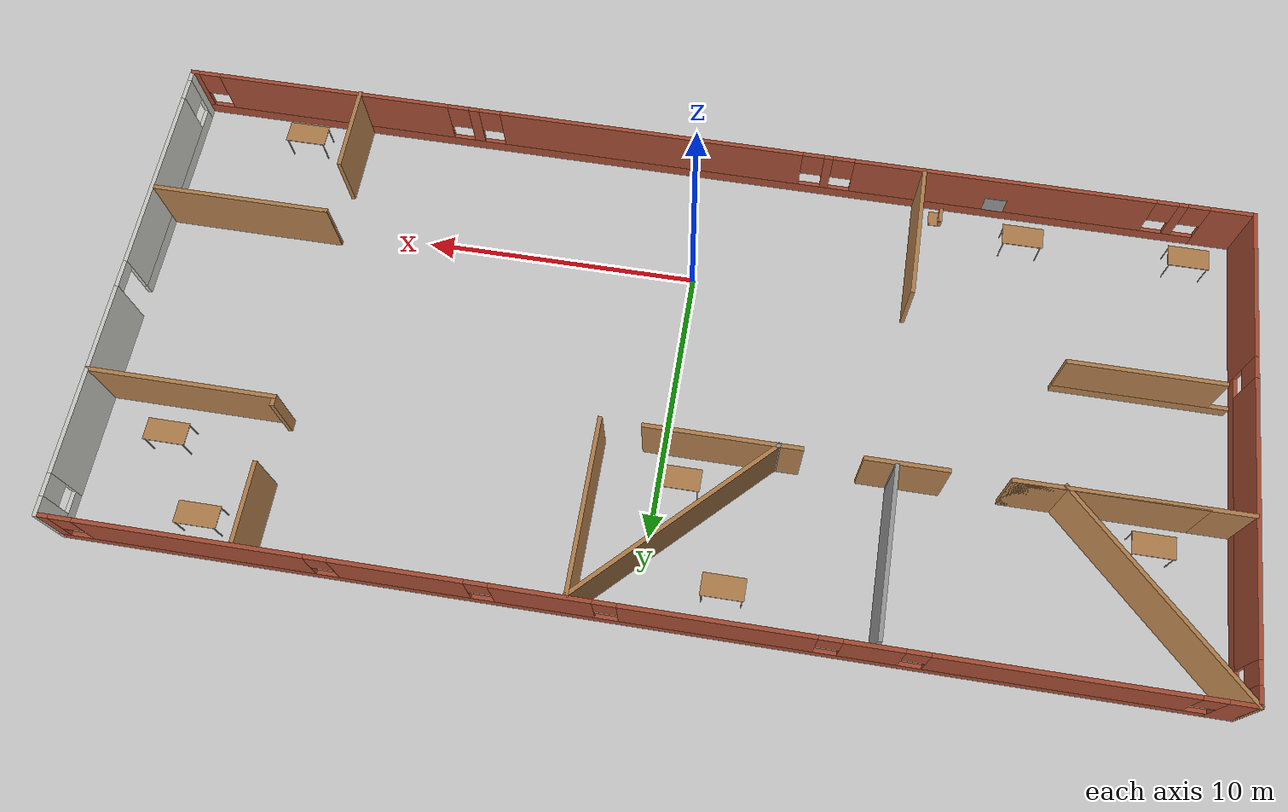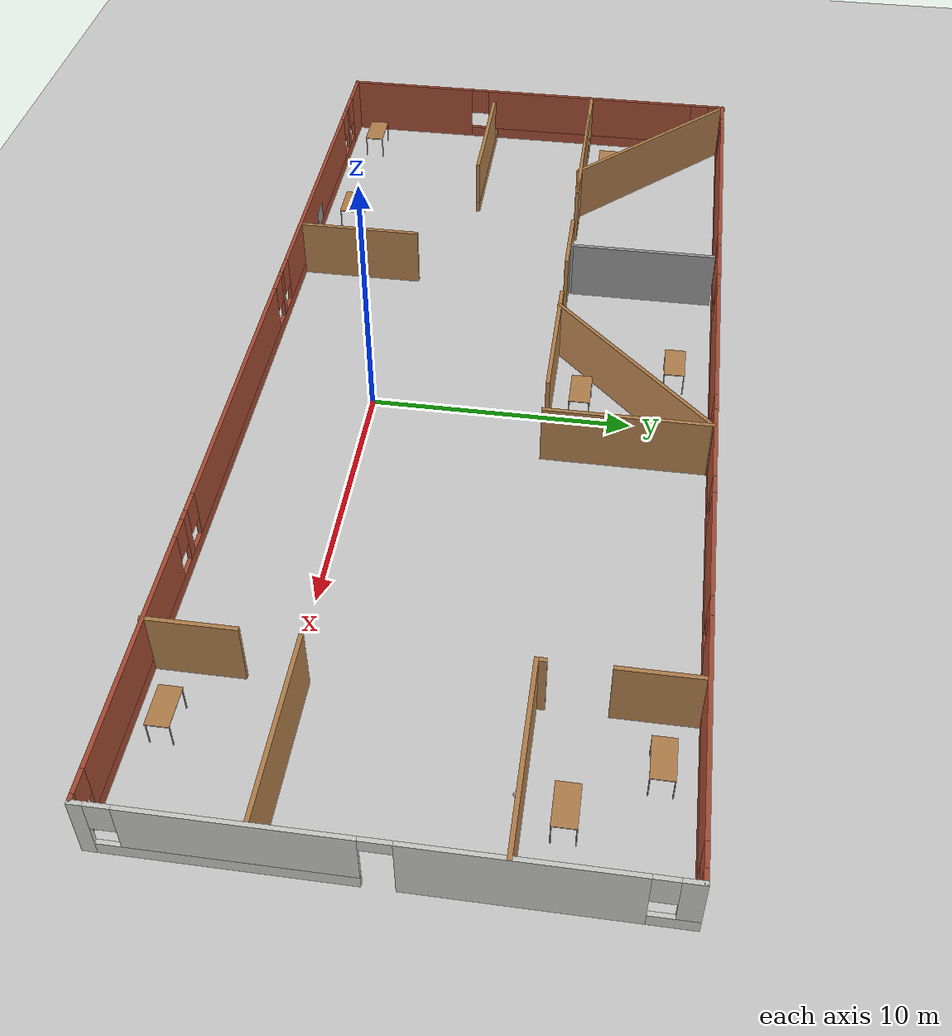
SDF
<sdf version="1.6">
 <world name="default">
  <plugin name="hello" filename="libhello.so"/>
  <light name="sun" type="directional">
   <pose>0 0 10 0 -0 0</pose>
   <diffuse>0.8 0.8 0.8 1</diffuse>
   <specular>0.2 0.2 0.2 1</specular>
   <attenuation>
    <range>1000</range>
    <constant>0.9</constant>
    <linear>0.01</linear>
    <quadratic>0.001</quadratic>
   </attenuation>
   <direction>-0.5 0.1 -0.9</direction>
  </light>
  <model name="ground_plane">
   <static>1</static>
   <link name="link">
    <collision name="collision">
     <geometry><plane><normal>0 0 1</normal><size>100 100</size></plane></geometry>
     <surface>
      <contact><collide_bitmask>65535</collide_bitmask></contact>
      <friction><ode><mu>100</mu><mu2>50</mu2></ode></friction>
     </surface>
    </collision>
    <visual name="visual">
     <cast_shadows>0</cast_shadows>
     <geometry><plane><normal>0 0 1</normal><size>100 100</size></plane></geometry>
     <material>
      <script><uri>file://media/materials/scripts/gazebo.material</uri><name>Gazebo/Grey</name></script>
     </material>
    </visual>
   </link>
  </model>
  <gravity>0 0 -9.8</gravity>
  <magnetic_field>6e-06 2.3e-05 -4.2e-05</magnetic_field>
  <atmosphere type="adiabatic"/>
  <physics name="default_physics" default="0" type="ode">
   <max_step_size>0.001</max_step_size>
   <real_time_factor>1</real_time_factor>
   <real_time_update_rate>1000</real_time_update_rate>
  </physics>
  <scene><ambient>0.4 0.4 0.4 1</ambient><background>0.7 0.7 0.7 1</background><shadows>1</shadows></scene>
  <spherical_coordinates>
   <surface_model>EARTH_WGS84</surface_model>
   <latitude_deg>0</latitude_deg>
   <longitude_deg>0</longitude_deg>
   <elevation>0</elevation>
   <heading_deg>0</heading_deg>
  </spherical_coordinates>
  <model name="table">
   <static>1</static>
   <link name="link">
    <collision name="surface">
     <pose>0 0 1 0 -0 0</pose>
     <geometry><box><size>1.5 0.8 0.03</size></box></geometry>
     <surface><friction><ode><mu>0.6</mu><mu2>0.6</mu2></ode></friction></surface>
    </collision>
    <visual name="visual1">
     <pose>0 0 1 0 -0 0</pose>
     <geometry><box><size>1.5 0.8 0.03</size></box></geometry>
     <material>
      <script><uri>file://media/materials/scripts/gazebo.material</uri><name>Gazebo/Wood</name></script>
     </material>
    </visual>
    <collision name="front_left_leg">
     <pose>0.68 0.38 0.5 0 -0 0</pose>
     <geometry><cylinder><radius>0.02</radius><length>1</length></cylinder></geometry>
    </collision>
    <visual name="front_left_leg">
     <pose>0.68 0.38 0.5 0 -0 0</pose>
     <geometry><cylinder><radius>0.02</radius><length>1</length></cylinder></geometry>
     <material>
      <script><uri>file://media/materials/scripts/gazebo.material</uri><name>Gazebo/Grey</name></script>
     </material>
    </visual>
    <collision name="front_right_leg">
     <pose>0.68 -0.38 0.5 0 -0 0</pose>
     <geometry><cylinder><radius>0.02</radius><length>1</length></cylinder></geometry>
    </collision>
    <visual name="front_right_leg">
     <pose>0.68 -0.38 0.5 0 -0 0</pose>
     <geometry><cylinder><radius>0.02</radius><length>1</length></cylinder></geometry>
     <material>
      <script><uri>file://media/materials/scripts/gazebo.material</uri><name>Gazebo/Grey</name></script>
     </material>
    </visual>
    <collision name="back_right_leg">
     <pose>-0.68 -0.38 0.5 0 -0 0</pose>
     <geometry><cylinder><radius>0.02</radius><length>1</length></cylinder></geometry>
    </collision>
    <visual name="back_right_leg">
     <pose>-0.68 -0.38 0.5 0 -0 0</pose>
     <geometry><cylinder><radius>0.02</radius><length>1</length></cylinder></geometry>
     <material>
      <script><uri>file://media/materials/scripts/gazebo.material</uri><name>Gazebo/Grey</name></script>
     </material>
    </visual>
    <collision name="back_left_leg">
     <pose>-0.68 0.38 0.5 0 -0 0</pose>
     <geometry><cylinder><radius>0.02</radius><length>1</length></cylinder></geometry>
    </collision>
    <visual name="back_left_leg">
     <pose>-0.68 0.38 0.5 0 -0 0</pose>
     <geometry><cylinder><radius>0.02</radius><length>1</length></cylinder></geometry>
     <material>
      <script><uri>file://media/materials/scripts/gazebo.material</uri><name>Gazebo/Grey</name></script>
     </material>
    </visual>
   </link>
   <pose>-2.77138 11.5368 0 0 -0 0</pose>
  </model>
  <model name="table_0">
   <static>1</static>
   <link name="link">
    <collision name="surface">
     <pose>0 0 1 0 -0 0</pose>
     <geometry><box><size>1.5 0.8 0.03</size></box></geometry>
     <surface><friction><ode><mu>0.6</mu><mu2>0.6</mu2></ode></friction></surface>
    </collision>
    <visual name="visual1">
     <pose>0 0 1 0 -0 0</pose>
     <geometry><box><size>1.5 0.8 0.03</size></box></geometry>
     <material>
      <script><uri>file://media/materials/scripts/gazebo.material</uri><name>Gazebo/Wood</name></script>
     </material>
    </visual>
    <collision name="front_left_leg">
     <pose>0.68 0.38 0.5 0 -0 0</pose>
     <geometry><cylinder><radius>0.02</radius><length>1</length></cylinder></geometry>
    </collision>
    <visual name="front_left_leg">
     <pose>0.68 0.38 0.5 0 -0 0</pose>
     <geometry><cylinder><radius>0.02</radius><length>1</length></cylinder></geometry>
     <material>
      <script><uri>file://media/materials/scripts/gazebo.material</uri><name>Gazebo/Grey</name></script>
     </material>
    </visual>
    <collision name="front_right_leg">
     <pose>0.68 -0.38 0.5 0 -0 0</pose>
     <geometry><cylinder><radius>0.02</radius><length>1</length></cylinder></geometry>
    </collision>
    <visual name="front_right_leg">
     <pose>0.68 -0.38 0.5 0 -0 0</pose>
     <geometry><cylinder><radius>0.02</radius><length>1</length></cylinder></geometry>
     <material>
      <script><uri>file://media/materials/scripts/gazebo.material</uri><name>Gazebo/Grey</name></script>
     </material>
    </visual>
    <collision name="back_right_leg">
     <pose>-0.68 -0.38 0.5 0 -0 0</pose>
     <geometry><cylinder><radius>0.02</radius><length>1</length></cylinder></geometry>
    </collision>
    <visual name="back_right_leg">
     <pose>-0.68 -0.38 0.5 0 -0 0</pose>
     <geometry><cylinder><radius>0.02</radius><length>1</length></cylinder></geometry>
     <material>
      <script><uri>file://media/materials/scripts/gazebo.material</uri><name>Gazebo/Grey</name></script>
     </material>
    </visual>
    <collision name="back_left_leg">
     <pose>-0.68 0.38 0.5 0 -0 0</pose>
     <geometry><cylinder><radius>0.02</radius><length>1</length></cylinder></geometry>
    </collision>
    <visual name="back_left_leg">
     <pose>-0.68 0.38 0.5 0 -0 0</pose>
     <geometry><cylinder><radius>0.02</radius><length>1</length></cylinder></geometry>
     <material>
      <script><uri>file://media/materials/scripts/gazebo.material</uri><name>Gazebo/Grey</name></script>
     </material>
    </visual>
   </link>
   <pose>-11.8478 -3.25901 0 0 -0 0</pose>
  </model>
  <model name="table_1">
   <static>1</static>
   <link name="link">
    <collision name="surface">
     <pose>0 0 1 0 -0 0</pose>
     <geometry><box><size>1.5 0.8 0.03</size></box></geometry>
     <surface><friction><ode><mu>0.6</mu><mu2>0.6</mu2></ode></friction></surface>
    </collision>
    <visual name="visual1">
     <pose>0 0 1 0 -0 0</pose>
     <geometry><box><size>1.5 0.8 0.03</size></box></geometry>
     <material>
      <script><uri>file://media/materials/scripts/gazebo.material</uri><name>Gazebo/Wood</name></script>
     </material>
    </visual>
    <collision name="front_left_leg">
     <pose>0.68 0.38 0.5 0 -0 0</pose>
     <geometry><cylinder><radius>0.02</radius><length>1</length></cylinder></geometry>
    </collision>
    <visual name="front_left_leg">
     <pose>0.68 0.38 0.5 0 -0 0</pose>
     <geometry><cylinder><radius>0.02</radius><length>1</length></cylinder></geometry>
     <material>
      <script><uri>file://media/materials/scripts/gazebo.material</uri><name>Gazebo/Grey</name></script>
     </material>
    </visual>
    <collision name="front_right_leg">
     <pose>0.68 -0.38 0.5 0 -0 0</pose>
     <geometry><cylinder><radius>0.02</radius><length>1</length></cylinder></geometry>
    </collision>
    <visual name="front_right_leg">
     <pose>0.68 -0.38 0.5 0 -0 0</pose>
     <geometry><cylinder><radius>0.02</radius><length>1</length></cylinder></geometry>
     <material>
      <script><uri>file://media/materials/scripts/gazebo.material</uri><name>Gazebo/Grey</name></script>
     </material>
    </visual>
    <collision name="back_right_leg">
     <pose>-0.68 -0.38 0.5 0 -0 0</pose>
     <geometry><cylinder><radius>0.02</radius><length>1</length></cylinder></geometry>
    </collision>
    <visual name="back_right_leg">
     <pose>-0.68 -0.38 0.5 0 -0 0</pose>
     <geometry><cylinder><radius>0.02</radius><length>1</length></cylinder></geometry>
     <material>
      <script><uri>file://media/materials/scripts/gazebo.material</uri><name>Gazebo/Grey</name></script>
     </material>
    </visual>
    <collision name="back_left_leg">
     <pose>-0.68 0.38 0.5 0 -0 0</pose>
     <geometry><cylinder><radius>0.02</radius><length>1</length></cylinder></geometry>
    </collision>
    <visual name="back_left_leg">
     <pose>-0.68 0.38 0.5 0 -0 0</pose>
     <geometry><cylinder><radius>0.02</radius><length>1</length></cylinder></geometry>
     <material>
      <script><uri>file://media/materials/scripts/gazebo.material</uri><name>Gazebo/Grey</name></script>
     </material>
    </visual>
   </link>
   <pose>-17.9186 -3.30988 0 0 -0 0</pose>
  </model>
  <model name="table_2">
   <static>1</static>
   <link name="link">
    <collision name="surface">
     <pose>0 0 1 0 -0 0</pose>
     <geometry><box><size>1.5 0.8 0.03</size></box></geometry>
     <surface><friction><ode><mu>0.6</mu><mu2>0.6</mu2></ode></friction></surface>
    </collision>
    <visual name="visual1">
     <pose>0 0 1 0 -0 0</pose>
     <geometry><box><size>1.5 0.8 0.03</size></box></geometry>
     <material>
      <script><uri>file://media/materials/scripts/gazebo.material</uri><name>Gazebo/Wood</name></script>
     </material>
    </visual>
    <collision name="front_left_leg">
     <pose>0.68 0.38 0.5 0 -0 0</pose>
     <geometry><cylinder><radius>0.02</radius><length>1</length></cylinder></geometry>
    </collision>
    <visual name="front_left_leg">
     <pose>0.68 0.38 0.5 0 -0 0</pose>
     <geometry><cylinder><radius>0.02</radius><length>1</length></cylinder></geometry>
     <material>
      <script><uri>file://media/materials/scripts/gazebo.material</uri><name>Gazebo/Grey</name></script>
     </material>
    </visual>
    <collision name="front_right_leg">
     <pose>0.68 -0.38 0.5 0 -0 0</pose>
     <geometry><cylinder><radius>0.02</radius><length>1</length></cylinder></geometry>
    </collision>
    <visual name="front_right_leg">
     <pose>0.68 -0.38 0.5 0 -0 0</pose>
     <geometry><cylinder><radius>0.02</radius><length>1</length></cylinder></geometry>
     <material>
      <script><uri>file://media/materials/scripts/gazebo.material</uri><name>Gazebo/Grey</name></script>
     </material>
    </visual>
    <collision name="back_right_leg">
     <pose>-0.68 -0.38 0.5 0 -0 0</pose>
     <geometry><cylinder><radius>0.02</radius><length>1</length></cylinder></geometry>
    </collision>
    <visual name="back_right_leg">
     <pose>-0.68 -0.38 0.5 0 -0 0</pose>
     <geometry><cylinder><radius>0.02</radius><length>1</length></cylinder></geometry>
     <material>
      <script><uri>file://media/materials/scripts/gazebo.material</uri><name>Gazebo/Grey</name></script>
     </material>
    </visual>
    <collision name="back_left_leg">
     <pose>-0.68 0.38 0.5 0 -0 0</pose>
     <geometry><cylinder><radius>0.02</radius><length>1</length></cylinder></geometry>
    </collision>
    <visual name="back_left_leg">
     <pose>-0.68 0.38 0.5 0 -0 0</pose>
     <geometry><cylinder><radius>0.02</radius><length>1</length></cylinder></geometry>
     <material>
      <script><uri>file://media/materials/scripts/gazebo.material</uri><name>Gazebo/Grey</name></script>
     </material>
    </visual>
   </link>
   <pose>-16.8726 7.8756 0 0 -0 0</pose>
  </model>
  <model name="table_3">
   <static>1</static>
   <link name="link">
    <collision name="surface">
     <pose>0 0 1 0 -0 0</pose>
     <geometry><box><size>1.5 0.8 0.03</size></box></geometry>
     <surface><friction><ode><mu>0.6</mu><mu2>0.6</mu2></ode></friction></surface>
    </collision>
    <visual name="visual1">
     <pose>0 0 1 0 -0 0</pose>
     <geometry><box><size>1.5 0.8 0.03</size></box></geometry>
     <material>
      <script><uri>file://media/materials/scripts/gazebo.material</uri><name>Gazebo/Wood</name></script>
     </material>
    </visual>
    <collision name="front_left_leg">
     <pose>0.68 0.38 0.5 0 -0 0</pose>
     <geometry><cylinder><radius>0.02</radius><length>1</length></cylinder></geometry>
    </collision>
    <visual name="front_left_leg">
     <pose>0.68 0.38 0.5 0 -0 0</pose>
     <geometry><cylinder><radius>0.02</radius><length>1</length></cylinder></geometry>
     <material>
      <script><uri>file://media/materials/scripts/gazebo.material</uri><name>Gazebo/Grey</name></script>
     </material>
    </visual>
    <collision name="front_right_leg">
     <pose>0.68 -0.38 0.5 0 -0 0</pose>
     <geometry><cylinder><radius>0.02</radius><length>1</length></cylinder></geometry>
    </collision>
    <visual name="front_right_leg">
     <pose>0.68 -0.38 0.5 0 -0 0</pose>
     <geometry><cylinder><radius>0.02</radius><length>1</length></cylinder></geometry>
     <material>
      <script><uri>file://media/materials/scripts/gazebo.material</uri><name>Gazebo/Grey</name></script>
     </material>
    </visual>
    <collision name="back_right_leg">
     <pose>-0.68 -0.38 0.5 0 -0 0</pose>
     <geometry><cylinder><radius>0.02</radius><length>1</length></cylinder></geometry>
    </collision>
    <visual name="back_right_leg">
     <pose>-0.68 -0.38 0.5 0 -0 0</pose>
     <geometry><cylinder><radius>0.02</radius><length>1</length></cylinder></geometry>
     <material>
      <script><uri>file://media/materials/scripts/gazebo.material</uri><name>Gazebo/Grey</name></script>
     </material>
    </visual>
    <collision name="back_left_leg">
     <pose>-0.68 0.38 0.5 0 -0 0</pose>
     <geometry><cylinder><radius>0.02</radius><length>1</length></cylinder></geometry>
    </collision>
    <visual name="back_left_leg">
     <pose>-0.68 0.38 0.5 0 -0 0</pose>
     <geometry><cylinder><radius>0.02</radius><length>1</length></cylinder></geometry>
     <material>
      <script><uri>file://media/materials/scripts/gazebo.material</uri><name>Gazebo/Grey</name></script>
     </material>
    </visual>
   </link>
   <pose>-0.746225 8.0046 0 0 -0 0</pose>
  </model>
  <model name="table_4">
   <static>1</static>
   <link name="link">
    <collision name="surface">
     <pose>0 0 1 0 -0 0</pose>
     <geometry><box><size>1.5 0.8 0.03</size></box></geometry>
     <surface><friction><ode><mu>0.6</mu><mu2>0.6</mu2></ode></friction></surface>
    </collision>
    <visual name="visual1">
     <pose>0 0 1 0 -0 0</pose>
     <geometry><box><size>1.5 0.8 0.03</size></box></geometry>
     <material>
      <script><uri>file://media/materials/scripts/gazebo.material</uri><name>Gazebo/Wood</name></script>
     </material>
    </visual>
    <collision name="front_left_leg">
     <pose>0.68 0.38 0.5 0 -0 0</pose>
     <geometry><cylinder><radius>0.02</radius><length>1</length></cylinder></geometry>
    </collision>
    <visual name="front_left_leg">
     <pose>0.68 0.38 0.5 0 -0 0</pose>
     <geometry><cylinder><radius>0.02</radius><length>1</length></cylinder></geometry>
     <material>
      <script><uri>file://media/materials/scripts/gazebo.material</uri><name>Gazebo/Grey</name></script>
     </material>
    </visual>
    <collision name="front_right_leg">
     <pose>0.68 -0.38 0.5 0 -0 0</pose>
     <geometry><cylinder><radius>0.02</radius><length>1</length></cylinder></geometry>
    </collision>
    <visual name="front_right_leg">
     <pose>0.68 -0.38 0.5 0 -0 0</pose>
     <geometry><cylinder><radius>0.02</radius><length>1</length></cylinder></geometry>
     <material>
      <script><uri>file://media/materials/scripts/gazebo.material</uri><name>Gazebo/Grey</name></script>
     </material>
    </visual>
    <collision name="back_right_leg">
     <pose>-0.68 -0.38 0.5 0 -0 0</pose>
     <geometry><cylinder><radius>0.02</radius><length>1</length></cylinder></geometry>
    </collision>
    <visual name="back_right_leg">
     <pose>-0.68 -0.38 0.5 0 -0 0</pose>
     <geometry><cylinder><radius>0.02</radius><length>1</length></cylinder></geometry>
     <material>
      <script><uri>file://media/materials/scripts/gazebo.material</uri><name>Gazebo/Grey</name></script>
     </material>
    </visual>
    <collision name="back_left_leg">
     <pose>-0.68 0.38 0.5 0 -0 0</pose>
     <geometry><cylinder><radius>0.02</radius><length>1</length></cylinder></geometry>
    </collision>
    <visual name="back_left_leg">
     <pose>-0.68 0.38 0.5 0 -0 0</pose>
     <geometry><cylinder><radius>0.02</radius><length>1</length></cylinder></geometry>
     <material>
      <script><uri>file://media/materials/scripts/gazebo.material</uri><name>Gazebo/Grey</name></script>
     </material>
    </visual>
   </link>
   <pose>17.1453 9.11903 0 0 -0 0</pose>
  </model>
  <model name="table_5">
   <static>1</static>
   <link name="link">
    <collision name="surface">
     <pose>0 0 1 0 -0 0</pose>
     <geometry><box><size>1.5 0.8 0.03</size></box></geometry>
     <surface><friction><ode><mu>0.6</mu><mu2>0.6</mu2></ode></friction></surface>
    </collision>
    <visual name="visual1">
     <pose>0 0 1 0 -0 0</pose>
     <geometry><box><size>1.5 0.8 0.03</size></box></geometry>
     <material>
      <script><uri>file://media/materials/scripts/gazebo.material</uri><name>Gazebo/Wood</name></script>
     </material>
    </visual>
    <collision name="front_left_leg">
     <pose>0.68 0.38 0.5 0 -0 0</pose>
     <geometry><cylinder><radius>0.02</radius><length>1</length></cylinder></geometry>
    </collision>
    <visual name="front_left_leg">
     <pose>0.68 0.38 0.5 0 -0 0</pose>
     <geometry><cylinder><radius>0.02</radius><length>1</length></cylinder></geometry>
     <material>
      <script><uri>file://media/materials/scripts/gazebo.material</uri><name>Gazebo/Grey</name></script>
     </material>
    </visual>
    <collision name="front_right_leg">
     <pose>0.68 -0.38 0.5 0 -0 0</pose>
     <geometry><cylinder><radius>0.02</radius><length>1</length></cylinder></geometry>
    </collision>
    <visual name="front_right_leg">
     <pose>0.68 -0.38 0.5 0 -0 0</pose>
     <geometry><cylinder><radius>0.02</radius><length>1</length></cylinder></geometry>
     <material>
      <script><uri>file://media/materials/scripts/gazebo.material</uri><name>Gazebo/Grey</name></script>
     </material>
    </visual>
    <collision name="back_right_leg">
     <pose>-0.68 -0.38 0.5 0 -0 0</pose>
     <geometry><cylinder><radius>0.02</radius><length>1</length></cylinder></geometry>
    </collision>
    <visual name="back_right_leg">
     <pose>-0.68 -0.38 0.5 0 -0 0</pose>
     <geometry><cylinder><radius>0.02</radius><length>1</length></cylinder></geometry>
     <material>
      <script><uri>file://media/materials/scripts/gazebo.material</uri><name>Gazebo/Grey</name></script>
     </material>
    </visual>
    <collision name="back_left_leg">
     <pose>-0.68 0.38 0.5 0 -0 0</pose>
     <geometry><cylinder><radius>0.02</radius><length>1</length></cylinder></geometry>
    </collision>
    <visual name="back_left_leg">
     <pose>-0.68 0.38 0.5 0 -0 0</pose>
     <geometry><cylinder><radius>0.02</radius><length>1</length></cylinder></geometry>
     <material>
      <script><uri>file://media/materials/scripts/gazebo.material</uri><name>Gazebo/Grey</name></script>
     </material>
    </visual>
   </link>
   <pose>15.2043 11.8509 0 0 -0 0</pose>
  </model>
  <model name="table_6">
   <static>1</static>
   <link name="link">
    <collision name="surface">
     <pose>0 0 1 0 -0 0</pose>
     <geometry><box><size>1.5 0.8 0.03</size></box></geometry>
     <surface><friction><ode><mu>0.6</mu><mu2>0.6</mu2></ode></friction></surface>
    </collision>
    <visual name="visual1">
     <pose>0 0 1 0 -0 0</pose>
     <geometry><box><size>1.5 0.8 0.03</size></box></geometry>
     <material>
      <script><uri>file://media/materials/scripts/gazebo.material</uri><name>Gazebo/Wood</name></script>
     </material>
    </visual>
    <collision name="front_left_leg">
     <pose>0.68 0.38 0.5 0 -0 0</pose>
     <geometry><cylinder><radius>0.02</radius><length>1</length></cylinder></geometry>
    </collision>
    <visual name="front_left_leg">
     <pose>0.68 0.38 0.5 0 -0 0</pose>
     <geometry><cylinder><radius>0.02</radius><length>1</length></cylinder></geometry>
     <material>
      <script><uri>file://media/materials/scripts/gazebo.material</uri><name>Gazebo/Grey</name></script>
     </material>
    </visual>
    <collision name="front_right_leg">
     <pose>0.68 -0.38 0.5 0 -0 0</pose>
     <geometry><cylinder><radius>0.02</radius><length>1</length></cylinder></geometry>
    </collision>
    <visual name="front_right_leg">
     <pose>0.68 -0.38 0.5 0 -0 0</pose>
     <geometry><cylinder><radius>0.02</radius><length>1</length></cylinder></geometry>
     <material>
      <script><uri>file://media/materials/scripts/gazebo.material</uri><name>Gazebo/Grey</name></script>
     </material>
    </visual>
    <collision name="back_right_leg">
     <pose>-0.68 -0.38 0.5 0 -0 0</pose>
     <geometry><cylinder><radius>0.02</radius><length>1</length></cylinder></geometry>
    </collision>
    <visual name="back_right_leg">
     <pose>-0.68 -0.38 0.5 0 -0 0</pose>
     <geometry><cylinder><radius>0.02</radius><length>1</length></cylinder></geometry>
     <material>
      <script><uri>file://media/materials/scripts/gazebo.material</uri><name>Gazebo/Grey</name></script>
     </material>
    </visual>
    <collision name="back_left_leg">
     <pose>-0.68 0.38 0.5 0 -0 0</pose>
     <geometry><cylinder><radius>0.02</radius><length>1</length></cylinder></geometry>
    </collision>
    <visual name="back_left_leg">
     <pose>-0.68 0.38 0.5 0 -0 0</pose>
     <geometry><cylinder><radius>0.02</radius><length>1</length></cylinder></geometry>
     <material>
      <script><uri>file://media/materials/scripts/gazebo.material</uri><name>Gazebo/Grey</name></script>
     </material>
    </visual>
   </link>
   <pose>15.4576 -3.44775 0 0 -0 0</pose>
  </model>
  <model name="wooden_case">
   <link name="base">
    <pose>0 0 0.024 0 -0 0</pose>
    <inertial>
     <pose>-0.022184 0 0.171592 0 -0 0</pose>
     <mass>3.96264</mass>
     <inertia>
      <ixx>0.213536</ixx>
      <ixy>0</ixy>
      <ixz>0.000779377</ixz>
      <iyy>0.0708943</iyy>
      <iyz>0</iyz>
      <izz>0.154604</izz>
     </inertia>
    </inertial>
    <collision name="collision_back">
     <pose>-0.053975 0 0.1778 0 -0 0</pose>
     <geometry><box><size>0.01905 0.5461 0.3175</size></box></geometry>
     <surface>
      <contact>
       <poissons_ratio>0.347</poissons_ratio>
       <elastic_modulus>8.8e+09</elastic_modulus>
       <ode><kp>100000</kp><kd>100</kd><max_vel>100</max_vel><min_depth>0.001</min_depth></ode>
      </contact>
      <friction>
       <torsional>
        <coefficient>1</coefficient>
        <use_patch_radius>0</use_patch_radius>
        <surface_radius>0.01</surface_radius>
       </torsional>
      </friction>
     </surface>
    </collision>
    <visual name="visual_back">
     <pose>-0.053975 0 0.1778 0 -0 0</pose>
     <geometry><box><size>0.01905 0.5461 0.3175</size></box></geometry>
     <material>
      <script><uri>file://media/materials/scripts/gazebo.material</uri><name>Gazebo/Wood</name></script>
     </material>
    </visual>
    <collision name="collision_bottom">
     <pose>0 0 0.009525 0 -0 0</pose>
     <geometry><box><size>0.127 0.5842 0.01905</size></box></geometry>
     <surface>
      <contact>
       <poissons_ratio>0.347</poissons_ratio>
       <elastic_modulus>8.8e+09</elastic_modulus>
       <ode><kp>100000</kp><kd>100</kd><max_vel>100</max_vel><min_depth>0.001</min_depth></ode>
      </contact>
      <friction>
       <torsional>
        <coefficient>1</coefficient>
        <use_patch_radius>0</use_patch_radius>
        <surface_radius>0.01</surface_radius>
       </torsional>
      </friction>
     </surface>
    </collision>
    <visual name="visual_bottom">
     <pose>0 0 0.009525 0 -0 0</pose>
     <geometry><box><size>0.127 0.5842 0.01905</size></box></geometry>
     <material>
      <script><uri>file://media/materials/scripts/gazebo.material</uri><name>Gazebo/Wood</name></script>
     </material>
    </visual>
    <collision name="collision_top">
     <pose>0 0 0.346075 0 -0 0</pose>
     <geometry><box><size>0.127 0.5842 0.01905</size></box></geometry>
     <surface>
      <contact>
       <poissons_ratio>0.347</poissons_ratio>
       <elastic_modulus>8.8e+09</elastic_modulus>
       <ode><kp>100000</kp><kd>100</kd><max_vel>100</max_vel><min_depth>0.001</min_depth></ode>
      </contact>
      <friction>
       <torsional>
        <coefficient>1</coefficient>
        <use_patch_radius>0</use_patch_radius>
        <surface_radius>0.01</surface_radius>
       </torsional>
      </friction>
     </surface>
    </collision>
    <visual name="visual_top">
     <pose>0 0 0.346075 0 -0 0</pose>
     <geometry><box><size>0.127 0.5842 0.01905</size></box></geometry>
     <material>
      <script><uri>file://media/materials/scripts/gazebo.material</uri><name>Gazebo/Wood</name></script>
     </material>
    </visual>
    <collision name="collision_left">
     <pose>0 -0.282575 0.1778 0 -0 0</pose>
     <geometry><box><size>0.127 0.01905 0.3175</size></box></geometry>
     <surface>
      <contact>
       <poissons_ratio>0.347</poissons_ratio>
       <elastic_modulus>8.8e+09</elastic_modulus>
       <ode><kp>100000</kp><kd>100</kd><max_vel>100</max_vel><min_depth>0.001</min_depth></ode>
      </contact>
      <friction>
       <torsional>
        <coefficient>1</coefficient>
        <use_patch_radius>0</use_patch_radius>
        <surface_radius>0.01</surface_radius>
       </torsional>
      </friction>
     </surface>
    </collision>
    <visual name="visual_left">
     <pose>0 -0.282575 0.1778 0 -0 0</pose>
     <geometry><box><size>0.127 0.01905 0.3175</size></box></geometry>
     <material>
      <script><uri>file://media/materials/scripts/gazebo.material</uri><name>Gazebo/Wood</name></script>
     </material>
    </visual>
    <collision name="collision_right">
     <pose>0 0.282575 0.1778 0 -0 0</pose>
     <geometry><box><size>0.127 0.01905 0.3175</size></box></geometry>
     <surface>
      <contact>
       <poissons_ratio>0.347</poissons_ratio>
       <elastic_modulus>8.8e+09</elastic_modulus>
       <ode><kp>100000</kp><kd>100</kd><max_vel>100</max_vel><min_depth>0.001</min_depth></ode>
      </contact>
      <friction>
       <torsional>
        <coefficient>1</coefficient>
        <use_patch_radius>0</use_patch_radius>
        <surface_radius>0.01</surface_radius>
       </torsional>
      </friction>
     </surface>
    </collision>
    <visual name="visual_right">
     <pose>0 0.282575 0.1778 0 -0 0</pose>
     <geometry><box><size>0.127 0.01905 0.3175</size></box></geometry>
     <material>
      <script><uri>file://media/materials/scripts/gazebo.material</uri><name>Gazebo/Wood</name></script>
     </material>
    </visual>
    <collision name="collision_block_left">
     <pose>0.0095 -0.2151 -0.012 0 -0 0</pose>
     <geometry><box><size>0.108 0.05 0.024</size></box></geometry>
     <surface>
      <contact>
       <poissons_ratio>0.347</poissons_ratio>
       <elastic_modulus>8.8e+09</elastic_modulus>
       <ode><kp>100000</kp><kd>100</kd><max_vel>100</max_vel><min_depth>0.001</min_depth></ode>
      </contact>
      <friction>
       <torsional>
        <coefficient>1</coefficient>
        <use_patch_radius>0</use_patch_radius>
        <surface_radius>0.01</surface_radius>
       </torsional>
      </friction>
     </surface>
    </collision>
    <visual name="visual_block_left">
     <pose>0.0095 -0.2151 -0.012 0 -0 0</pose>
     <geometry><box><size>0.108 0.05 0.024</size></box></geometry>
     <material>
      <script><uri>file://media/materials/scripts/gazebo.material</uri><name>Gazebo/Wood</name></script>
     </material>
    </visual>
    <collision name="collision_block_right">
     <pose>0.0095 0.2151 -0.012 0 -0 0</pose>
     <geometry><box><size>0.108 0.05 0.024</size></box></geometry>
     <surface>
      <contact>
       <poissons_ratio>0.347</poissons_ratio>
       <elastic_modulus>8.8e+09</elastic_modulus>
       <ode><kp>100000</kp><kd>100</kd><max_vel>100</max_vel><min_depth>0.001</min_depth></ode>
      </contact>
      <friction>
       <torsional>
        <coefficient>1</coefficient>
        <use_patch_radius>0</use_patch_radius>
        <surface_radius>0.01</surface_radius>
       </torsional>
      </friction>
     </surface>
    </collision>
    <visual name="visual_block_right">
     <pose>0.0095 0.2151 -0.012 0 -0 0</pose>
     <geometry><box><size>0.108 0.05 0.024</size></box></geometry>
     <material>
      <script><uri>file://media/materials/scripts/gazebo.material</uri><name>Gazebo/Wood</name></script>
     </material>
    </visual>
   </link>
   <link name="lid">
    <pose>0.243775 0 0.009525 0 -0 0</pose>
    <inertial>
     <mass>1.97874</mass>
     <inertia>
      <ixx>0.0563367</ixx>
      <ixy>0</ixy>
      <ixz>0</ixz>
      <iyy>0.020911</iyy>
      <iyz>0</iyz>
      <izz>0.0771281</izz>
     </inertia>
    </inertial>
    <collision name="collision">
     <geometry><box><size>0.3556 0.5842 0.01905</size></box></geometry>
     <surface>
      <contact>
       <poissons_ratio>0.347</poissons_ratio>
       <elastic_modulus>8.8e+09</elastic_modulus>
       <ode><kp>100000</kp><kd>100</kd><max_vel>100</max_vel><min_depth>0.001</min_depth></ode>
      </contact>
      <friction>
       <torsional>
        <coefficient>1</coefficient>
        <use_patch_radius>0</use_patch_radius>
        <surface_radius>0.01</surface_radius>
       </torsional>
      </friction>
     </surface>
    </collision>
    <visual name="visual">
     <geometry><box><size>0.3556 0.5842 0.01905</size></box></geometry>
     <material>
      <script><uri>file://media/materials/scripts/gazebo.material</uri><name>Gazebo/Wood</name></script>
     </material>
    </visual>
    <visual name="tee_nut_1">
     <pose>0.122 -0.216 0 0 -0 0</pose>
     <geometry><cylinder><radius>0.00635</radius><length>0.0192405</length></cylinder></geometry>
     <material>
      <script><uri>file://media/materials/scripts/gazebo.material</uri><name>Gazebo/Grey</name></script>
     </material>
    </visual>
    <visual name="tee_nut_2">
     <pose>0.122 -0.088 0 0 -0 0</pose>
     <geometry><cylinder><radius>0.00635</radius><length>0.0192405</length></cylinder></geometry>
     <material>
      <script><uri>file://media/materials/scripts/gazebo.material</uri><name>Gazebo/Grey</name></script>
     </material>
    </visual>
    <visual name="tee_nut_3">
     <pose>0.122 0.088 0 0 -0 0</pose>
     <geometry><cylinder><radius>0.00635</radius><length>0.0192405</length></cylinder></geometry>
     <material>
      <script><uri>file://media/materials/scripts/gazebo.material</uri><name>Gazebo/Grey</name></script>
     </material>
    </visual>
    <visual name="tee_nut_4">
     <pose>0.122 0.216 0 0 -0 0</pose>
     <geometry><cylinder><radius>0.00635</radius><length>0.0192405</length></cylinder></geometry>
     <material>
      <script><uri>file://media/materials/scripts/gazebo.material</uri><name>Gazebo/Grey</name></script>
     </material>
    </visual>
   </link>
   <joint name="lid_hinge" type="revolute">
    <pose>-0.1778 0 0.01905 0 -0 0</pose>
    <parent>base</parent>
    <child>lid</child>
    <axis>
     <xyz>0 1 0</xyz>
     <limit><upper>0.523599</upper><lower>-1.5708</lower></limit>
     <use_parent_model_frame>0</use_parent_model_frame>
     <dynamics><spring_reference>0</spring_reference><spring_stiffness>0</spring_stiffness></dynamics>
    </axis>
   </joint>
   <pose>-8.86546 -4.06321 -0.001057 0 -0.000428 -1e-06</pose>
  </model>
  <model name="mybuilding">
   <link name="Wall_28">
    <pose>0.015532 -8.79244 0 0 -0 0</pose>
    <visual name="Wall_28_Visual_0">
     <pose>-19.0594 0 1.25 0 -0 0</pose>
     <geometry><box><size>1.65971 0.15 2.5</size></box></geometry>
     <material>
      <script><uri>file://media/materials/scripts/gazebo.material</uri><name>Gazebo/Bricks</name></script>
      <ambient>1 1 1 1</ambient>
      <shader type="pixel"/>
      <diffuse>1 1 1 1</diffuse>
      <specular>0.2 0.2 0.2 1</specular>
      <emissive>0 0 0 1</emissive>
     </material>
     <meta><layer>0</layer></meta>
    </visual>
    <visual name="Wall_28_Visual_1">
     <pose>0.829853 0 0.25 0 -0 0</pose>
     <geometry><box><size>38.1188 0.15 0.5</size></box></geometry>
     <material>
      <script><uri>file://media/materials/scripts/gazebo.material</uri><name>Gazebo/Bricks</name></script>
      <ambient>1 1 1 1</ambient>
      <shader type="pixel"/>
      <diffuse>1 1 1 1</diffuse>
      <specular>0.2 0.2 0.2 1</specular>
      <emissive>0 0 0 1</emissive>
     </material>
     <meta><layer>0</layer></meta>
    </visual>
    <visual name="Wall_28_Visual_2">
     <pose>-17.26 0 1.5 0 -0 0</pose>
     <geometry><box><size>0.339006 0.15 2</size></box></geometry>
     <material>
      <script><uri>file://media/materials/scripts/gazebo.material</uri><name>Gazebo/Bricks</name></script>
      <ambient>1 1 1 1</ambient>
      <shader type="pixel"/>
      <diffuse>1 1 1 1</diffuse>
      <specular>0.2 0.2 0.2 1</specular>
      <emissive>0 0 0 1</emissive>
     </material>
     <meta><layer>0</layer></meta>
    </visual>
    <visual name="Wall_28_Visual_3">
     <pose>-10.8105 0 1.5 0 -0 0</pose>
     <geometry><box><size>10.96 0.15 2</size></box></geometry>
     <material>
      <script><uri>file://media/materials/scripts/gazebo.material</uri><name>Gazebo/Bricks</name></script>
      <ambient>1 1 1 1</ambient>
      <shader type="pixel"/>
      <diffuse>1 1 1 1</diffuse>
      <specular>0.2 0.2 0.2 1</specular>
      <emissive>0 0 0 1</emissive>
     </material>
     <meta><layer>0</layer></meta>
    </visual>
    <visual name="Wall_28_Visual_4">
     <pose>-4.37053 0 1.5 0 -0 0</pose>
     <geometry><box><size>0.32 0.15 2</size></box></geometry>
     <material>
      <script><uri>file://media/materials/scripts/gazebo.material</uri><name>Gazebo/Bricks</name></script>
      <ambient>1 1 1 1</ambient>
      <shader type="pixel"/>
      <diffuse>1 1 1 1</diffuse>
      <specular>0.2 0.2 0.2 1</specular>
      <emissive>0 0 0 1</emissive>
     </material>
     <meta><layer>0</layer></meta>
    </visual>
    <visual name="Wall_28_Visual_5">
     <pose>2.26947 0 1.5 0 -0 0</pose>
     <geometry><box><size>11.36 0.15 2</size></box></geometry>
     <material>
      <script><uri>file://media/materials/scripts/gazebo.material</uri><name>Gazebo/Bricks</name></script>
      <ambient>1 1 1 1</ambient>
      <shader type="pixel"/>
      <diffuse>1 1 1 1</diffuse>
      <specular>0.2 0.2 0.2 1</specular>
      <emissive>0 0 0 1</emissive>
     </material>
     <meta><layer>0</layer></meta>
    </visual>
    <visual name="Wall_28_Visual_6">
     <pose>8.94947 0 1.5 0 -0 0</pose>
     <geometry><box><size>0.4 0.15 2</size></box></geometry>
     <material>
      <script><uri>file://media/materials/scripts/gazebo.material</uri><name>Gazebo/Bricks</name></script>
      <ambient>1 1 1 1</ambient>
      <shader type="pixel"/>
      <diffuse>1 1 1 1</diffuse>
      <specular>0.2 0.2 0.2 1</specular>
      <emissive>0 0 0 1</emissive>
     </material>
     <meta><layer>0</layer></meta>
    </visual>
    <visual name="Wall_28_Visual_7">
     <pose>14.3495 0 1.5 0 -0 0</pose>
     <geometry><box><size>8.8 0.15 2</size></box></geometry>
     <material>
      <script><uri>file://media/materials/scripts/gazebo.material</uri><name>Gazebo/Bricks</name></script>
      <ambient>1 1 1 1</ambient>
      <shader type="pixel"/>
      <diffuse>1 1 1 1</diffuse>
      <specular>0.2 0.2 0.2 1</specular>
      <emissive>0 0 0 1</emissive>
     </material>
     <meta><layer>0</layer></meta>
    </visual>
    <visual name="Wall_28_Visual_8">
     <pose>19.7194 0 1.5 0 -0 0</pose>
     <geometry><box><size>0.339765 0.15 2</size></box></geometry>
     <material>
      <script><uri>file://media/materials/scripts/gazebo.material</uri><name>Gazebo/Bricks</name></script>
      <ambient>1 1 1 1</ambient>
      <shader type="pixel"/>
      <diffuse>1 1 1 1</diffuse>
      <specular>0.2 0.2 0.2 1</specular>
      <emissive>0 0 0 1</emissive>
     </material>
     <meta><layer>0</layer></meta>
    </visual>
    <visual name="Wall_28_Visual_9">
     <pose>-17.8295 0 1.9 0 -0 0</pose>
     <geometry><box><size>0.8 0.15 1.2</size></box></geometry>
     <material>
      <script><uri>file://media/materials/scripts/gazebo.material</uri><name>Gazebo/Bricks</name></script>
      <ambient>1 1 1 1</ambient>
      <shader type="pixel"/>
      <diffuse>1 1 1 1</diffuse>
      <specular>0.2 0.2 0.2 1</specular>
      <emissive>0 0 0 1</emissive>
     </material>
     <meta><layer>0</layer></meta>
    </visual>
    <visual name="Wall_28_Visual_10">
     <pose>-16.6905 0 1.9 0 -0 0</pose>
     <geometry><box><size>0.8 0.15 1.2</size></box></geometry>
     <material>
      <script><uri>file://media/materials/scripts/gazebo.material</uri><name>Gazebo/Bricks</name></script>
      <ambient>1 1 1 1</ambient>
      <shader type="pixel"/>
      <diffuse>1 1 1 1</diffuse>
      <specular>0.2 0.2 0.2 1</specular>
      <emissive>0 0 0 1</emissive>
     </material>
     <meta><layer>0</layer></meta>
    </visual>
    <visual name="Wall_28_Visual_11">
     <pose>-4.93053 0 1.9 0 -0 0</pose>
     <geometry><box><size>0.8 0.15 1.2</size></box></geometry>
     <material>
      <script><uri>file://media/materials/scripts/gazebo.material</uri><name>Gazebo/Bricks</name></script>
      <ambient>1 1 1 1</ambient>
      <shader type="pixel"/>
      <diffuse>1 1 1 1</diffuse>
      <specular>0.2 0.2 0.2 1</specular>
      <emissive>0 0 0 1</emissive>
     </material>
     <meta><layer>0</layer></meta>
    </visual>
    <visual name="Wall_28_Visual_12">
     <pose>-3.81053 0 1.9 0 -0 0</pose>
     <geometry><box><size>0.8 0.15 1.2</size></box></geometry>
     <material>
      <script><uri>file://media/materials/scripts/gazebo.material</uri><name>Gazebo/Bricks</name></script>
      <ambient>1 1 1 1</ambient>
      <shader type="pixel"/>
      <diffuse>1 1 1 1</diffuse>
      <specular>0.2 0.2 0.2 1</specular>
      <emissive>0 0 0 1</emissive>
     </material>
     <meta><layer>0</layer></meta>
    </visual>
    <visual name="Wall_28_Visual_13">
     <pose>8.34947 0 1.9 0 -0 0</pose>
     <geometry><box><size>0.8 0.15 1.2</size></box></geometry>
     <material>
      <script><uri>file://media/materials/scripts/gazebo.material</uri><name>Gazebo/Bricks</name></script>
      <ambient>1 1 1 1</ambient>
      <shader type="pixel"/>
      <diffuse>1 1 1 1</diffuse>
      <specular>0.2 0.2 0.2 1</specular>
      <emissive>0 0 0 1</emissive>
     </material>
     <meta><layer>0</layer></meta>
    </visual>
    <visual name="Wall_28_Visual_14">
     <pose>9.54947 0 1.9 0 -0 0</pose>
     <geometry><box><size>0.8 0.15 1.2</size></box></geometry>
     <material>
      <script><uri>file://media/materials/scripts/gazebo.material</uri><name>Gazebo/Bricks</name></script>
      <ambient>1 1 1 1</ambient>
      <shader type="pixel"/>
      <diffuse>1 1 1 1</diffuse>
      <specular>0.2 0.2 0.2 1</specular>
      <emissive>0 0 0 1</emissive>
     </material>
     <meta><layer>0</layer></meta>
    </visual>
    <visual name="Wall_28_Visual_15">
     <pose>19.1495 0 1.9 0 -0 0</pose>
     <geometry><box><size>0.8 0.15 1.2</size></box></geometry>
     <material>
      <script><uri>file://media/materials/scripts/gazebo.material</uri><name>Gazebo/Bricks</name></script>
      <ambient>1 1 1 1</ambient>
      <shader type="pixel"/>
      <diffuse>1 1 1 1</diffuse>
      <specular>0.2 0.2 0.2 1</specular>
      <emissive>0 0 0 1</emissive>
     </material>
     <meta><layer>0</layer></meta>
    </visual>
    <collision name="Wall_28_Collision_0">
     <pose>-19.0594 0 1.25 0 -0 0</pose>
     <geometry><box><size>1.65971 0.15 2.5</size></box></geometry>
     <surface>
      <friction>
       <ode><mu>1</mu><mu2>1</mu2><fdir1>0 0 0</fdir1><slip1>0</slip1><slip2>0</slip2></ode>
       <torsional>
        <coefficient>1</coefficient>
        <patch_radius>0</patch_radius>
        <surface_radius>0</surface_radius>
        <use_patch_radius>1</use_patch_radius>
        <ode><slip>0</slip></ode>
       </torsional>
      </friction>
      <bounce><restitution_coefficient>0</restitution_coefficient><threshold>1e+06</threshold></bounce>
      <contact>
       <collide_without_contact>0</collide_without_contact>
       <collide_without_contact_bitmask>1</collide_without_contact_bitmask>
       <collide_bitmask>1</collide_bitmask>
       <ode>
        <soft_cfm>0</soft_cfm>
        <soft_erp>0.2</soft_erp>
        <kp>1e+13</kp>
        <kd>1</kd>
        <max_vel>0.01</max_vel>
        <min_depth>0</min_depth>
       </ode>
       <bullet>
        <split_impulse>1</split_impulse>
        <split_impulse_penetration_threshold>-0.01</split_impulse_penetration_threshold>
        <soft_cfm>0</soft_cfm>
        <soft_erp>0.2</soft_erp>
        <kp>1e+13</kp>
        <kd>1</kd>
       </bullet>
      </contact>
     </surface>
    </collision>
    <collision name="Wall_28_Collision_1">
     <pose>0.829853 0 0.25 0 -0 0</pose>
     <geometry><box><size>38.1188 0.15 0.5</size></box></geometry>
     <surface>
      <friction>
       <ode><mu>1</mu><mu2>1</mu2><fdir1>0 0 0</fdir1><slip1>0</slip1><slip2>0</slip2></ode>
       <torsional>
        <coefficient>1</coefficient>
        <patch_radius>0</patch_radius>
        <surface_radius>0</surface_radius>
        <use_patch_radius>1</use_patch_radius>
        <ode><slip>0</slip></ode>
       </torsional>
      </friction>
      <bounce><restitution_coefficient>0</restitution_coefficient><threshold>1e+06</threshold></bounce>
      <contact>
       <collide_without_contact>0</collide_without_contact>
       <collide_without_contact_bitmask>1</collide_without_contact_bitmask>
       <collide_bitmask>1</collide_bitmask>
       <ode>
        <soft_cfm>0</soft_cfm>
        <soft_erp>0.2</soft_erp>
        <kp>1e+13</kp>
        <kd>1</kd>
        <max_vel>0.01</max_vel>
        <min_depth>0</min_depth>
       </ode>
       <bullet>
        <split_impulse>1</split_impulse>
        <split_impulse_penetration_threshold>-0.01</split_impulse_penetration_threshold>
        <soft_cfm>0</soft_cfm>
        <soft_erp>0.2</soft_erp>
        <kp>1e+13</kp>
        <kd>1</kd>
       </bullet>
      </contact>
     </surface>
    </collision>
    <collision name="Wall_28_Collision_2">
     <pose>-17.26 0 1.5 0 -0 0</pose>
     <geometry><box><size>0.339006 0.15 2</size></box></geometry>
     <surface>
      <friction>
       <ode><mu>1</mu><mu2>1</mu2><fdir1>0 0 0</fdir1><slip1>0</slip1><slip2>0</slip2></ode>
       <torsional>
        <coefficient>1</coefficient>
        <patch_radius>0</patch_radius>
        <surface_radius>0</surface_radius>
        <use_patch_radius>1</use_patch_radius>
        <ode><slip>0</slip></ode>
       </torsional>
      </friction>
      <bounce><restitution_coefficient>0</restitution_coefficient><threshold>1e+06</threshold></bounce>
      <contact>
       <collide_without_contact>0</collide_without_contact>
       <collide_without_contact_bitmask>1</collide_without_contact_bitmask>
       <collide_bitmask>1</collide_bitmask>
       <ode>
        <soft_cfm>0</soft_cfm>
        <soft_erp>0.2</soft_erp>
        <kp>1e+13</kp>
        <kd>1</kd>
        <max_vel>0.01</max_vel>
        <min_depth>0</min_depth>
       </ode>
       <bullet>
        <split_impulse>1</split_impulse>
        <split_impulse_penetration_threshold>-0.01</split_impulse_penetration_threshold>
        <soft_cfm>0</soft_cfm>
        <soft_erp>0.2</soft_erp>
        <kp>1e+13</kp>
        <kd>1</kd>
       </bullet>
      </contact>
     </surface>
    </collision>
    <collision name="Wall_28_Collision_3">
     <pose>-10.8105 0 1.5 0 -0 0</pose>
     <geometry><box><size>10.96 0.15 2</size></box></geometry>
     <surface>
      <friction>
       <ode><mu>1</mu><mu2>1</mu2><fdir1>0 0 0</fdir1><slip1>0</slip1><slip2>0</slip2></ode>
       <torsional>
        <coefficient>1</coefficient>
        <patch_radius>0</patch_radius>
        <surface_radius>0</surface_radius>
        <use_patch_radius>1</use_patch_radius>
        <ode><slip>0</slip></ode>
       </torsional>
      </friction>
      <bounce><restitution_coefficient>0</restitution_coefficient><threshold>1e+06</threshold></bounce>
      <contact>
       <collide_without_contact>0</collide_without_contact>
       <collide_without_contact_bitmask>1</collide_without_contact_bitmask>
       <collide_bitmask>1</collide_bitmask>
       <ode>
        <soft_cfm>0</soft_cfm>
        <soft_erp>0.2</soft_erp>
        <kp>1e+13</kp>
        <kd>1</kd>
        <max_vel>0.01</max_vel>
        <min_depth>0</min_depth>
       </ode>
       <bullet>
        <split_impulse>1</split_impulse>
        <split_impulse_penetration_threshold>-0.01</split_impulse_penetration_threshold>
        <soft_cfm>0</soft_cfm>
        <soft_erp>0.2</soft_erp>
        <kp>1e+13</kp>
        <kd>1</kd>
       </bullet>
      </contact>
     </surface>
    </collision>
    <collision name="Wall_28_Collision_4">
     <pose>-4.37053 0 1.5 0 -0 0</pose>
     <geometry><box><size>0.32 0.15 2</size></box></geometry>
     <surface>
      <friction>
       <ode><mu>1</mu><mu2>1</mu2><fdir1>0 0 0</fdir1><slip1>0</slip1><slip2>0</slip2></ode>
       <torsional>
        <coefficient>1</coefficient>
        <patch_radius>0</patch_radius>
        <surface_radius>0</surface_radius>
        <use_patch_radius>1</use_patch_radius>
        <ode><slip>0</slip></ode>
       </torsional>
      </friction>
      <bounce><restitution_coefficient>0</restitution_coefficient><threshold>1e+06</threshold></bounce>
      <contact>
       <collide_without_contact>0</collide_without_contact>
       <collide_without_contact_bitmask>1</collide_without_contact_bitmask>
       <collide_bitmask>1</collide_bitmask>
       <ode>
        <soft_cfm>0</soft_cfm>
        <soft_erp>0.2</soft_erp>
        <kp>1e+13</kp>
        <kd>1</kd>
        <max_vel>0.01</max_vel>
        <min_depth>0</min_depth>
       </ode>
       <bullet>
        <split_impulse>1</split_impulse>
        <split_impulse_penetration_threshold>-0.01</split_impulse_penetration_threshold>
        <soft_cfm>0</soft_cfm>
        <soft_erp>0.2</soft_erp>
        <kp>1e+13</kp>
        <kd>1</kd>
       </bullet>
      </contact>
     </surface>
    </collision>
    <collision name="Wall_28_Collision_5">
     <pose>2.26947 0 1.5 0 -0 0</pose>
     <geometry><box><size>11.36 0.15 2</size></box></geometry>
     <surface>
      <friction>
       <ode><mu>1</mu><mu2>1</mu2><fdir1>0 0 0</fdir1><slip1>0</slip1><slip2>0</slip2></ode>
       <torsional>
        <coefficient>1</coefficient>
        <patch_radius>0</patch_radius>
        <surface_radius>0</surface_radius>
        <use_patch_radius>1</use_patch_radius>
        <ode><slip>0</slip></ode>
       </torsional>
      </friction>
      <bounce><restitution_coefficient>0</restitution_coefficient><threshold>1e+06</threshold></bounce>
      <contact>
       <collide_without_contact>0</collide_without_contact>
       <collide_without_contact_bitmask>1</collide_without_contact_bitmask>
       <collide_bitmask>1</collide_bitmask>
       <ode>
        <soft_cfm>0</soft_cfm>
        <soft_erp>0.2</soft_erp>
        <kp>1e+13</kp>
        <kd>1</kd>
        <max_vel>0.01</max_vel>
        <min_depth>0</min_depth>
       </ode>
       <bullet>
        <split_impulse>1</split_impulse>
        <split_impulse_penetration_threshold>-0.01</split_impulse_penetration_threshold>
        <soft_cfm>0</soft_cfm>
        <soft_erp>0.2</soft_erp>
        <kp>1e+13</kp>
        <kd>1</kd>
       </bullet>
      </contact>
     </surface>
    </collision>
    <collision name="Wall_28_Collision_6">
     <pose>8.94947 0 1.5 0 -0 0</pose>
     <geometry><box><size>0.4 0.15 2</size></box></geometry>
     <surface>
      <friction>
       <ode><mu>1</mu><mu2>1</mu2><fdir1>0 0 0</fdir1><slip1>0</slip1><slip2>0</slip2></ode>
       <torsional>
        <coefficient>1</coefficient>
        <patch_radius>0</patch_radius>
        <surface_radius>0</surface_radius>
        <use_patch_radius>1</use_patch_radius>
        <ode><slip>0</slip></ode>
       </torsional>
      </friction>
      <bounce><restitution_coefficient>0</restitution_coefficient><threshold>1e+06</threshold></bounce>
      <contact>
       <collide_without_contact>0</collide_without_contact>
       <collide_without_contact_bitmask>1</collide_without_contact_bitmask>
       <collide_bitmask>1</collide_bitmask>
       <ode>
        <soft_cfm>0</soft_cfm>
        <soft_erp>0.2</soft_erp>
        <kp>1e+13</kp>
        <kd>1</kd>
        <max_vel>0.01</max_vel>
        <min_depth>0</min_depth>
       </ode>
       <bullet>
        <split_impulse>1</split_impulse>
        <split_impulse_penetration_threshold>-0.01</split_impulse_penetration_threshold>
        <soft_cfm>0</soft_cfm>
        <soft_erp>0.2</soft_erp>
        <kp>1e+13</kp>
        <kd>1</kd>
       </bullet>
      </contact>
     </surface>
    </collision>
    <collision name="Wall_28_Collision_7">
     <pose>14.3495 0 1.5 0 -0 0</pose>
     <geometry><box><size>8.8 0.15 2</size></box></geometry>
     <surface>
      <friction>
       <ode><mu>1</mu><mu2>1</mu2><fdir1>0 0 0</fdir1><slip1>0</slip1><slip2>0</slip2></ode>
       <torsional>
        <coefficient>1</coefficient>
        <patch_radius>0</patch_radius>
        <surface_radius>0</surface_radius>
        <use_patch_radius>1</use_patch_radius>
        <ode><slip>0</slip></ode>
       </torsional>
      </friction>
      <bounce><restitution_coefficient>0</restitution_coefficient><threshold>1e+06</threshold></bounce>
      <contact>
       <collide_without_contact>0</collide_without_contact>
       <collide_without_contact_bitmask>1</collide_without_contact_bitmask>
       <collide_bitmask>1</collide_bitmask>
       <ode>
        <soft_cfm>0</soft_cfm>
        <soft_erp>0.2</soft_erp>
        <kp>1e+13</kp>
        <kd>1</kd>
        <max_vel>0.01</max_vel>
        <min_depth>0</min_depth>
       </ode>
       <bullet>
        <split_impulse>1</split_impulse>
        <split_impulse_penetration_threshold>-0.01</split_impulse_penetration_threshold>
        <soft_cfm>0</soft_cfm>
        <soft_erp>0.2</soft_erp>
        <kp>1e+13</kp>
        <kd>1</kd>
       </bullet>
      </contact>
     </surface>
    </collision>
    <collision name="Wall_28_Collision_8">
     <pose>19.7194 0 1.5 0 -0 0</pose>
     <geometry><box><size>0.339765 0.15 2</size></box></geometry>
     <surface>
      <friction>
       <ode><mu>1</mu><mu2>1</mu2><fdir1>0 0 0</fdir1><slip1>0</slip1><slip2>0</slip2></ode>
       <torsional>
        <coefficient>1</coefficient>
        <patch_radius>0</patch_radius>
        <surface_radius>0</surface_radius>
        <use_patch_radius>1</use_patch_radius>
        <ode><slip>0</slip></ode>
       </torsional>
      </friction>
      <bounce><restitution_coefficient>0</restitution_coefficient><threshold>1e+06</threshold></bounce>
      <contact>
       <collide_without_contact>0</collide_without_contact>
       <collide_without_contact_bitmask>1</collide_without_contact_bitmask>
       <collide_bitmask>1</collide_bitmask>
       <ode>
        <soft_cfm>0</soft_cfm>
        <soft_erp>0.2</soft_erp>
        <kp>1e+13</kp>
        <kd>1</kd>
        <max_vel>0.01</max_vel>
        <min_depth>0</min_depth>
       </ode>
       <bullet>
        <split_impulse>1</split_impulse>
        <split_impulse_penetration_threshold>-0.01</split_impulse_penetration_threshold>
        <soft_cfm>0</soft_cfm>
        <soft_erp>0.2</soft_erp>
        <kp>1e+13</kp>
        <kd>1</kd>
       </bullet>
      </contact>
     </surface>
    </collision>
    <collision name="Wall_28_Collision_9">
     <pose>-17.8295 0 1.9 0 -0 0</pose>
     <geometry><box><size>0.8 0.15 1.2</size></box></geometry>
     <surface>
      <friction>
       <ode><mu>1</mu><mu2>1</mu2><fdir1>0 0 0</fdir1><slip1>0</slip1><slip2>0</slip2></ode>
       <torsional>
        <coefficient>1</coefficient>
        <patch_radius>0</patch_radius>
        <surface_radius>0</surface_radius>
        <use_patch_radius>1</use_patch_radius>
        <ode><slip>0</slip></ode>
       </torsional>
      </friction>
      <bounce><restitution_coefficient>0</restitution_coefficient><threshold>1e+06</threshold></bounce>
      <contact>
       <collide_without_contact>0</collide_without_contact>
       <collide_without_contact_bitmask>1</collide_without_contact_bitmask>
       <collide_bitmask>1</collide_bitmask>
       <ode>
        <soft_cfm>0</soft_cfm>
        <soft_erp>0.2</soft_erp>
        <kp>1e+13</kp>
        <kd>1</kd>
        <max_vel>0.01</max_vel>
        <min_depth>0</min_depth>
       </ode>
       <bullet>
        <split_impulse>1</split_impulse>
        <split_impulse_penetration_threshold>-0.01</split_impulse_penetration_threshold>
        <soft_cfm>0</soft_cfm>
        <soft_erp>0.2</soft_erp>
        <kp>1e+13</kp>
        <kd>1</kd>
       </bullet>
      </contact>
     </surface>
    </collision>
    <collision name="Wall_28_Collision_11">
     <pose>-4.93053 0 1.9 0 -0 0</pose>
     <geometry><box><size>0.8 0.15 1.2</size></box></geometry>
     <surface>
      <friction>
       <ode><mu>1</mu><mu2>1</mu2><fdir1>0 0 0</fdir1><slip1>0</slip1><slip2>0</slip2></ode>
       <torsional>
        <coefficient>1</coefficient>
        <patch_radius>0</patch_radius>
        <surface_radius>0</surface_radius>
        <use_patch_radius>1</use_patch_radius>
        <ode><slip>0</slip></ode>
       </torsional>
      </friction>
      <bounce><restitution_coefficient>0</restitution_coefficient><threshold>1e+06</threshold></bounce>
      <contact>
       <collide_without_contact>0</collide_without_contact>
       <collide_without_contact_bitmask>1</collide_without_contact_bitmask>
       <collide_bitmask>1</collide_bitmask>
       <ode>
        <soft_cfm>0</soft_cfm>
        <soft_erp>0.2</soft_erp>
        <kp>1e+13</kp>
        <kd>1</kd>
        <max_vel>0.01</max_vel>
        <min_depth>0</min_depth>
       </ode>
       <bullet>
        <split_impulse>1</split_impulse>
        <split_impulse_penetration_threshold>-0.01</split_impulse_penetration_threshold>
        <soft_cfm>0</soft_cfm>
        <soft_erp>0.2</soft_erp>
        <kp>1e+13</kp>
        <kd>1</kd>
       </bullet>
      </contact>
     </surface>
    </collision>
    <collision name="Wall_28_Collision_10">
     <pose>-16.6905 0 1.9 0 -0 0</pose>
     <geometry><box><size>0.8 0.15 1.2</size></box></geometry>
     <surface>
      <friction>
       <ode><mu>1</mu><mu2>1</mu2><fdir1>0 0 0</fdir1><slip1>0</slip1><slip2>0</slip2></ode>
       <torsional>
        <coefficient>1</coefficient>
        <patch_radius>0</patch_radius>
        <surface_radius>0</surface_radius>
        <use_patch_radius>1</use_patch_radius>
        <ode><slip>0</slip></ode>
       </torsional>
      </friction>
      <bounce><restitution_coefficient>0</restitution_coefficient><threshold>1e+06</threshold></bounce>
      <contact>
       <collide_without_contact>0</collide_without_contact>
       <collide_without_contact_bitmask>1</collide_without_contact_bitmask>
       <collide_bitmask>1</collide_bitmask>
       <ode>
        <soft_cfm>0</soft_cfm>
        <soft_erp>0.2</soft_erp>
        <kp>1e+13</kp>
        <kd>1</kd>
        <max_vel>0.01</max_vel>
        <min_depth>0</min_depth>
       </ode>
       <bullet>
        <split_impulse>1</split_impulse>
        <split_impulse_penetration_threshold>-0.01</split_impulse_penetration_threshold>
        <soft_cfm>0</soft_cfm>
        <soft_erp>0.2</soft_erp>
        <kp>1e+13</kp>
        <kd>1</kd>
       </bullet>
      </contact>
     </surface>
    </collision>
    <collision name="Wall_28_Collision_12">
     <pose>-3.81053 0 1.9 0 -0 0</pose>
     <geometry><box><size>0.8 0.15 1.2</size></box></geometry>
     <surface>
      <friction>
       <ode><mu>1</mu><mu2>1</mu2><fdir1>0 0 0</fdir1><slip1>0</slip1><slip2>0</slip2></ode>
       <torsional>
        <coefficient>1</coefficient>
        <patch_radius>0</patch_radius>
        <surface_radius>0</surface_radius>
        <use_patch_radius>1</use_patch_radius>
        <ode><slip>0</slip></ode>
       </torsional>
      </friction>
      <bounce><restitution_coefficient>0</restitution_coefficient><threshold>1e+06</threshold></bounce>
      <contact>
       <collide_without_contact>0</collide_without_contact>
       <collide_without_contact_bitmask>1</collide_without_contact_bitmask>
       <collide_bitmask>1</collide_bitmask>
       <ode>
        <soft_cfm>0</soft_cfm>
        <soft_erp>0.2</soft_erp>
        <kp>1e+13</kp>
        <kd>1</kd>
        <max_vel>0.01</max_vel>
        <min_depth>0</min_depth>
       </ode>
       <bullet>
        <split_impulse>1</split_impulse>
        <split_impulse_penetration_threshold>-0.01</split_impulse_penetration_threshold>
        <soft_cfm>0</soft_cfm>
        <soft_erp>0.2</soft_erp>
        <kp>1e+13</kp>
        <kd>1</kd>
       </bullet>
      </contact>
     </surface>
    </collision>
    <collision name="Wall_28_Collision_14">
     <pose>9.54947 0 1.9 0 -0 0</pose>
     <geometry><box><size>0.8 0.15 1.2</size></box></geometry>
     <surface>
      <friction>
       <ode><mu>1</mu><mu2>1</mu2><fdir1>0 0 0</fdir1><slip1>0</slip1><slip2>0</slip2></ode>
       <torsional>
        <coefficient>1</coefficient>
        <patch_radius>0</patch_radius>
        <surface_radius>0</surface_radius>
        <use_patch_radius>1</use_patch_radius>
        <ode><slip>0</slip></ode>
       </torsional>
      </friction>
      <bounce><restitution_coefficient>0</restitution_coefficient><threshold>1e+06</threshold></bounce>
      <contact>
       <collide_without_contact>0</collide_without_contact>
       <collide_without_contact_bitmask>1</collide_without_contact_bitmask>
       <collide_bitmask>1</collide_bitmask>
       <ode>
        <soft_cfm>0</soft_cfm>
        <soft_erp>0.2</soft_erp>
        <kp>1e+13</kp>
        <kd>1</kd>
        <max_vel>0.01</max_vel>
        <min_depth>0</min_depth>
       </ode>
       <bullet>
        <split_impulse>1</split_impulse>
        <split_impulse_penetration_threshold>-0.01</split_impulse_penetration_threshold>
        <soft_cfm>0</soft_cfm>
        <soft_erp>0.2</soft_erp>
        <kp>1e+13</kp>
        <kd>1</kd>
       </bullet>
      </contact>
     </surface>
    </collision>
    <collision name="Wall_28_Collision_13">
     <pose>8.34947 0 1.9 0 -0 0</pose>
     <geometry><box><size>0.8 0.15 1.2</size></box></geometry>
     <surface>
      <friction>
       <ode><mu>1</mu><mu2>1</mu2><fdir1>0 0 0</fdir1><slip1>0</slip1><slip2>0</slip2></ode>
       <torsional>
        <coefficient>1</coefficient>
        <patch_radius>0</patch_radius>
        <surface_radius>0</surface_radius>
        <use_patch_radius>1</use_patch_radius>
        <ode><slip>0</slip></ode>
       </torsional>
      </friction>
      <bounce><restitution_coefficient>0</restitution_coefficient><threshold>1e+06</threshold></bounce>
      <contact>
       <collide_without_contact>0</collide_without_contact>
       <collide_without_contact_bitmask>1</collide_without_contact_bitmask>
       <collide_bitmask>1</collide_bitmask>
       <ode>
        <soft_cfm>0</soft_cfm>
        <soft_erp>0.2</soft_erp>
        <kp>1e+13</kp>
        <kd>1</kd>
        <max_vel>0.01</max_vel>
        <min_depth>0</min_depth>
       </ode>
       <bullet>
        <split_impulse>1</split_impulse>
        <split_impulse_penetration_threshold>-0.01</split_impulse_penetration_threshold>
        <soft_cfm>0</soft_cfm>
        <soft_erp>0.2</soft_erp>
        <kp>1e+13</kp>
        <kd>1</kd>
       </bullet>
      </contact>
     </surface>
    </collision>
    <collision name="Wall_28_Collision_15">
     <pose>19.1495 0 1.9 0 -0 0</pose>
     <geometry><box><size>0.8 0.15 1.2</size></box></geometry>
     <surface>
      <friction>
       <ode><mu>1</mu><mu2>1</mu2><fdir1>0 0 0</fdir1><slip1>0</slip1><slip2>0</slip2></ode>
       <torsional>
        <coefficient>1</coefficient>
        <patch_radius>0</patch_radius>
        <surface_radius>0</surface_radius>
        <use_patch_radius>1</use_patch_radius>
        <ode><slip>0</slip></ode>
       </torsional>
      </friction>
      <bounce><restitution_coefficient>0</restitution_coefficient><threshold>1e+06</threshold></bounce>
      <contact>
       <collide_without_contact>0</collide_without_contact>
       <collide_without_contact_bitmask>1</collide_without_contact_bitmask>
       <collide_bitmask>1</collide_bitmask>
       <ode>
        <soft_cfm>0</soft_cfm>
        <soft_erp>0.2</soft_erp>
        <kp>1e+13</kp>
        <kd>1</kd>
        <max_vel>0.01</max_vel>
        <min_depth>0</min_depth>
       </ode>
       <bullet>
        <split_impulse>1</split_impulse>
        <split_impulse_penetration_threshold>-0.01</split_impulse_penetration_threshold>
        <soft_cfm>0</soft_cfm>
        <soft_erp>0.2</soft_erp>
        <kp>1e+13</kp>
        <kd>1</kd>
       </bullet>
      </contact>
     </surface>
    </collision>
   </link>
   <link name="Wall_41">
    <pose>19.8298 0.007562 0 0 -0 1.5708</pose>
    <visual name="Wall_41_Visual_9">
     <pose>-0.150712 0 2.25 0 -0 0</pose>
     <geometry><box><size>1 0.15 0.5</size></box></geometry>
     <material>
      <script><uri>file://media/materials/scripts/gazebo.material</uri><name>Gazebo/CeilingTiled</name></script>
      <ambient>1 0.972549 0.847059 1</ambient>
      <shader type="pixel"/>
      <diffuse>1 1 1 1</diffuse>
      <specular>0 0 0 1</specular>
      <emissive>0 0 0 1</emissive>
     </material>
     <meta><layer>0</layer></meta>
    </visual>
    <visual name="Wall_41_Visual_0">
     <pose>-8.63665 0 1.25 0 -0 0</pose>
     <geometry><box><size>0.476697 0.15 2.5</size></box></geometry>
     <material>
      <script><uri>file://media/materials/scripts/gazebo.material</uri><name>Gazebo/CeilingTiled</name></script>
      <ambient>1 0.972549 0.847059 1</ambient>
      <shader type="pixel"/>
      <diffuse>1 1 1 1</diffuse>
      <specular>0 0 0 1</specular>
      <emissive>0 0 0 1</emissive>
     </material>
     <meta><layer>0</layer></meta>
    </visual>
    <visual name="Wall_41_Visual_1">
     <pose>3.85638 0 1.25 0 -0 0</pose>
     <geometry><box><size>7.01419 0.15 2.5</size></box></geometry>
     <material>
      <script><uri>file://media/materials/scripts/gazebo.material</uri><name>Gazebo/CeilingTiled</name></script>
      <ambient>1 0.972549 0.847059 1</ambient>
      <shader type="pixel"/>
      <diffuse>1 1 1 1</diffuse>
      <specular>0 0 0 1</specular>
      <emissive>0 0 0 1</emissive>
     </material>
     <meta><layer>0</layer></meta>
    </visual>
    <visual name="Wall_41_Visual_2">
     <pose>-4.52451 0 0.25 0 -0 0</pose>
     <geometry><box><size>7.74759 0.15 0.5</size></box></geometry>
     <material>
      <script><uri>file://media/materials/scripts/gazebo.material</uri><name>Gazebo/CeilingTiled</name></script>
      <ambient>1 0.972549 0.847059 1</ambient>
      <shader type="pixel"/>
      <diffuse>1 1 1 1</diffuse>
      <specular>0 0 0 1</specular>
      <emissive>0 0 0 1</emissive>
     </material>
     <meta><layer>0</layer></meta>
    </visual>
    <visual name="Wall_41_Visual_3">
     <pose>8.11924 0 0.25 0 -0 0</pose>
     <geometry><box><size>1.51152 0.15 0.5</size></box></geometry>
     <material>
      <script><uri>file://media/materials/scripts/gazebo.material</uri><name>Gazebo/CeilingTiled</name></script>
      <ambient>1 0.972549 0.847059 1</ambient>
      <shader type="pixel"/>
      <diffuse>1 1 1 1</diffuse>
      <specular>0 0 0 1</specular>
      <emissive>0 0 0 1</emissive>
     </material>
     <meta><layer>0</layer></meta>
    </visual>
    <visual name="Wall_41_Visual_4">
     <pose>-4.12451 0 1.5 0 -0 0</pose>
     <geometry><box><size>6.94759 0.15 2</size></box></geometry>
     <material>
      <script><uri>file://media/materials/scripts/gazebo.material</uri><name>Gazebo/CeilingTiled</name></script>
      <ambient>1 0.972549 0.847059 1</ambient>
      <shader type="pixel"/>
      <diffuse>1 1 1 1</diffuse>
      <specular>0 0 0 1</specular>
      <emissive>0 0 0 1</emissive>
     </material>
     <meta><layer>0</layer></meta>
    </visual>
    <visual name="Wall_41_Visual_5">
     <pose>-4.12451 0 1.5 0 -0 0</pose>
     <geometry><box><size>6.94759 0.15 2</size></box></geometry>
     <material>
      <script><uri>file://media/materials/scripts/gazebo.material</uri><name>Gazebo/CeilingTiled</name></script>
      <ambient>1 0.972549 0.847059 1</ambient>
      <shader type="pixel"/>
      <diffuse>1 1 1 1</diffuse>
      <specular>0 0 0 1</specular>
      <emissive>0 0 0 1</emissive>
     </material>
     <meta><layer>0</layer></meta>
    </visual>
    <visual name="Wall_41_Visual_6">
     <pose>8.51924 0 1.5 0 -0 0</pose>
     <geometry><box><size>0.711521 0.15 2</size></box></geometry>
     <material>
      <script><uri>file://media/materials/scripts/gazebo.material</uri><name>Gazebo/CeilingTiled</name></script>
      <ambient>1 0.972549 0.847059 1</ambient>
      <shader type="pixel"/>
      <diffuse>1 1 1 1</diffuse>
      <specular>0 0 0 1</specular>
      <emissive>0 0 0 1</emissive>
     </material>
     <meta><layer>0</layer></meta>
    </visual>
    <visual name="Wall_41_Visual_7">
     <pose>-7.9983 0 1.9 0 -0 0</pose>
     <geometry><box><size>0.8 0.15 1.2</size></box></geometry>
     <material>
      <script><uri>file://media/materials/scripts/gazebo.material</uri><name>Gazebo/CeilingTiled</name></script>
      <ambient>1 0.972549 0.847059 1</ambient>
      <shader type="pixel"/>
      <diffuse>1 1 1 1</diffuse>
      <specular>0 0 0 1</specular>
      <emissive>0 0 0 1</emissive>
     </material>
     <meta><layer>0</layer></meta>
    </visual>
    <visual name="Wall_41_Visual_8">
     <pose>7.76348 0 1.9 0 -0 0</pose>
     <geometry><box><size>0.8 0.15 1.2</size></box></geometry>
     <material>
      <script><uri>file://media/materials/scripts/gazebo.material</uri><name>Gazebo/CeilingTiled</name></script>
      <ambient>1 0.972549 0.847059 1</ambient>
      <shader type="pixel"/>
      <diffuse>1 1 1 1</diffuse>
      <specular>0 0 0 1</specular>
      <emissive>0 0 0 1</emissive>
     </material>
     <meta><layer>0</layer></meta>
    </visual>
    <visual name="Wall_41_Visual_10">
     <pose>-0.150712 0 2.25 0 -0 0</pose>
     <geometry><box><size>1 0.15 0.5</size></box></geometry>
     <material>
      <script><uri>file://media/materials/scripts/gazebo.material</uri><name>Gazebo/CeilingTiled</name></script>
      <ambient>1 0.972549 0.847059 1</ambient>
      <shader type="pixel"/>
      <diffuse>1 1 1 1</diffuse>
      <specular>0 0 0 1</specular>
      <emissive>0 0 0 1</emissive>
     </material>
     <meta><layer>0</layer></meta>
    </visual>
    <collision name="Wall_41_Collision_0">
     <pose>-8.63665 0 1.25 0 -0 0</pose>
     <geometry><box><size>0.476697 0.15 2.5</size></box></geometry>
     <surface>
      <friction>
       <ode><mu>1</mu><mu2>1</mu2><fdir1>0 0 0</fdir1><slip1>0</slip1><slip2>0</slip2></ode>
       <torsional>
        <coefficient>1</coefficient>
        <patch_radius>0</patch_radius>
        <surface_radius>0</surface_radius>
        <use_patch_radius>1</use_patch_radius>
        <ode><slip>0</slip></ode>
       </torsional>
      </friction>
      <bounce><restitution_coefficient>0</restitution_coefficient><threshold>1e+06</threshold></bounce>
      <contact>
       <collide_without_contact>0</collide_without_contact>
       <collide_without_contact_bitmask>1</collide_without_contact_bitmask>
       <collide_bitmask>1</collide_bitmask>
       <ode>
        <soft_cfm>0</soft_cfm>
        <soft_erp>0.2</soft_erp>
        <kp>1e+13</kp>
        <kd>1</kd>
        <max_vel>0.01</max_vel>
        <min_depth>0</min_depth>
       </ode>
       <bullet>
        <split_impulse>1</split_impulse>
        <split_impulse_penetration_threshold>-0.01</split_impulse_penetration_threshold>
        <soft_cfm>0</soft_cfm>
        <soft_erp>0.2</soft_erp>
        <kp>1e+13</kp>
        <kd>1</kd>
       </bullet>
      </contact>
     </surface>
    </collision>
    <collision name="Wall_41_Collision_1">
     <pose>3.85638 0 1.25 0 -0 0</pose>
     <geometry><box><size>7.01419 0.15 2.5</size></box></geometry>
     <surface>
      <friction>
       <ode><mu>1</mu><mu2>1</mu2><fdir1>0 0 0</fdir1><slip1>0</slip1><slip2>0</slip2></ode>
       <torsional>
        <coefficient>1</coefficient>
        <patch_radius>0</patch_radius>
        <surface_radius>0</surface_radius>
        <use_patch_radius>1</use_patch_radius>
        <ode><slip>0</slip></ode>
       </torsional>
      </friction>
      <bounce><restitution_coefficient>0</restitution_coefficient><threshold>1e+06</threshold></bounce>
      <contact>
       <collide_without_contact>0</collide_without_contact>
       <collide_without_contact_bitmask>1</collide_without_contact_bitmask>
       <collide_bitmask>1</collide_bitmask>
       <ode>
        <soft_cfm>0</soft_cfm>
        <soft_erp>0.2</soft_erp>
        <kp>1e+13</kp>
        <kd>1</kd>
        <max_vel>0.01</max_vel>
        <min_depth>0</min_depth>
       </ode>
       <bullet>
        <split_impulse>1</split_impulse>
        <split_impulse_penetration_threshold>-0.01</split_impulse_penetration_threshold>
        <soft_cfm>0</soft_cfm>
        <soft_erp>0.2</soft_erp>
        <kp>1e+13</kp>
        <kd>1</kd>
       </bullet>
      </contact>
     </surface>
    </collision>
    <collision name="Wall_41_Collision_2">
     <pose>-4.52451 0 0.25 0 -0 0</pose>
     <geometry><box><size>7.74759 0.15 0.5</size></box></geometry>
     <surface>
      <friction>
       <ode><mu>1</mu><mu2>1</mu2><fdir1>0 0 0</fdir1><slip1>0</slip1><slip2>0</slip2></ode>
       <torsional>
        <coefficient>1</coefficient>
        <patch_radius>0</patch_radius>
        <surface_radius>0</surface_radius>
        <use_patch_radius>1</use_patch_radius>
        <ode><slip>0</slip></ode>
       </torsional>
      </friction>
      <bounce><restitution_coefficient>0</restitution_coefficient><threshold>1e+06</threshold></bounce>
      <contact>
       <collide_without_contact>0</collide_without_contact>
       <collide_without_contact_bitmask>1</collide_without_contact_bitmask>
       <collide_bitmask>1</collide_bitmask>
       <ode>
        <soft_cfm>0</soft_cfm>
        <soft_erp>0.2</soft_erp>
        <kp>1e+13</kp>
        <kd>1</kd>
        <max_vel>0.01</max_vel>
        <min_depth>0</min_depth>
       </ode>
       <bullet>
        <split_impulse>1</split_impulse>
        <split_impulse_penetration_threshold>-0.01</split_impulse_penetration_threshold>
        <soft_cfm>0</soft_cfm>
        <soft_erp>0.2</soft_erp>
        <kp>1e+13</kp>
        <kd>1</kd>
       </bullet>
      </contact>
     </surface>
    </collision>
    <collision name="Wall_41_Collision_3">
     <pose>8.11924 0 0.25 0 -0 0</pose>
     <geometry><box><size>1.51152 0.15 0.5</size></box></geometry>
     <surface>
      <friction>
       <ode><mu>1</mu><mu2>1</mu2><fdir1>0 0 0</fdir1><slip1>0</slip1><slip2>0</slip2></ode>
       <torsional>
        <coefficient>1</coefficient>
        <patch_radius>0</patch_radius>
        <surface_radius>0</surface_radius>
        <use_patch_radius>1</use_patch_radius>
        <ode><slip>0</slip></ode>
       </torsional>
      </friction>
      <bounce><restitution_coefficient>0</restitution_coefficient><threshold>1e+06</threshold></bounce>
      <contact>
       <collide_without_contact>0</collide_without_contact>
       <collide_without_contact_bitmask>1</collide_without_contact_bitmask>
       <collide_bitmask>1</collide_bitmask>
       <ode>
        <soft_cfm>0</soft_cfm>
        <soft_erp>0.2</soft_erp>
        <kp>1e+13</kp>
        <kd>1</kd>
        <max_vel>0.01</max_vel>
        <min_depth>0</min_depth>
       </ode>
       <bullet>
        <split_impulse>1</split_impulse>
        <split_impulse_penetration_threshold>-0.01</split_impulse_penetration_threshold>
        <soft_cfm>0</soft_cfm>
        <soft_erp>0.2</soft_erp>
        <kp>1e+13</kp>
        <kd>1</kd>
       </bullet>
      </contact>
     </surface>
    </collision>
    <collision name="Wall_41_Collision_4">
     <pose>-4.12451 0 1.5 0 -0 0</pose>
     <geometry><box><size>6.94759 0.15 2</size></box></geometry>
     <surface>
      <friction>
       <ode><mu>1</mu><mu2>1</mu2><fdir1>0 0 0</fdir1><slip1>0</slip1><slip2>0</slip2></ode>
       <torsional>
        <coefficient>1</coefficient>
        <patch_radius>0</patch_radius>
        <surface_radius>0</surface_radius>
        <use_patch_radius>1</use_patch_radius>
        <ode><slip>0</slip></ode>
       </torsional>
      </friction>
      <bounce><restitution_coefficient>0</restitution_coefficient><threshold>1e+06</threshold></bounce>
      <contact>
       <collide_without_contact>0</collide_without_contact>
       <collide_without_contact_bitmask>1</collide_without_contact_bitmask>
       <collide_bitmask>1</collide_bitmask>
       <ode>
        <soft_cfm>0</soft_cfm>
        <soft_erp>0.2</soft_erp>
        <kp>1e+13</kp>
        <kd>1</kd>
        <max_vel>0.01</max_vel>
        <min_depth>0</min_depth>
       </ode>
       <bullet>
        <split_impulse>1</split_impulse>
        <split_impulse_penetration_threshold>-0.01</split_impulse_penetration_threshold>
        <soft_cfm>0</soft_cfm>
        <soft_erp>0.2</soft_erp>
        <kp>1e+13</kp>
        <kd>1</kd>
       </bullet>
      </contact>
     </surface>
    </collision>
    <collision name="Wall_41_Collision_5">
     <pose>-4.12451 0 1.5 0 -0 0</pose>
     <geometry><box><size>6.94759 0.15 2</size></box></geometry>
     <surface>
      <friction>
       <ode><mu>1</mu><mu2>1</mu2><fdir1>0 0 0</fdir1><slip1>0</slip1><slip2>0</slip2></ode>
       <torsional>
        <coefficient>1</coefficient>
        <patch_radius>0</patch_radius>
        <surface_radius>0</surface_radius>
        <use_patch_radius>1</use_patch_radius>
        <ode><slip>0</slip></ode>
       </torsional>
      </friction>
      <bounce><restitution_coefficient>0</restitution_coefficient><threshold>1e+06</threshold></bounce>
      <contact>
       <collide_without_contact>0</collide_without_contact>
       <collide_without_contact_bitmask>1</collide_without_contact_bitmask>
       <collide_bitmask>1</collide_bitmask>
       <ode>
        <soft_cfm>0</soft_cfm>
        <soft_erp>0.2</soft_erp>
        <kp>1e+13</kp>
        <kd>1</kd>
        <max_vel>0.01</max_vel>
        <min_depth>0</min_depth>
       </ode>
       <bullet>
        <split_impulse>1</split_impulse>
        <split_impulse_penetration_threshold>-0.01</split_impulse_penetration_threshold>
        <soft_cfm>0</soft_cfm>
        <soft_erp>0.2</soft_erp>
        <kp>1e+13</kp>
        <kd>1</kd>
       </bullet>
      </contact>
     </surface>
    </collision>
    <collision name="Wall_41_Collision_6">
     <pose>8.51924 0 1.5 0 -0 0</pose>
     <geometry><box><size>0.711521 0.15 2</size></box></geometry>
     <surface>
      <friction>
       <ode><mu>1</mu><mu2>1</mu2><fdir1>0 0 0</fdir1><slip1>0</slip1><slip2>0</slip2></ode>
       <torsional>
        <coefficient>1</coefficient>
        <patch_radius>0</patch_radius>
        <surface_radius>0</surface_radius>
        <use_patch_radius>1</use_patch_radius>
        <ode><slip>0</slip></ode>
       </torsional>
      </friction>
      <bounce><restitution_coefficient>0</restitution_coefficient><threshold>1e+06</threshold></bounce>
      <contact>
       <collide_without_contact>0</collide_without_contact>
       <collide_without_contact_bitmask>1</collide_without_contact_bitmask>
       <collide_bitmask>1</collide_bitmask>
       <ode>
        <soft_cfm>0</soft_cfm>
        <soft_erp>0.2</soft_erp>
        <kp>1e+13</kp>
        <kd>1</kd>
        <max_vel>0.01</max_vel>
        <min_depth>0</min_depth>
       </ode>
       <bullet>
        <split_impulse>1</split_impulse>
        <split_impulse_penetration_threshold>-0.01</split_impulse_penetration_threshold>
        <soft_cfm>0</soft_cfm>
        <soft_erp>0.2</soft_erp>
        <kp>1e+13</kp>
        <kd>1</kd>
       </bullet>
      </contact>
     </surface>
    </collision>
    <collision name="Wall_41_Collision_7">
     <pose>-7.9983 0 1.9 0 -0 0</pose>
     <geometry><box><size>0.8 0.15 1.2</size></box></geometry>
     <surface>
      <friction>
       <ode><mu>1</mu><mu2>1</mu2><fdir1>0 0 0</fdir1><slip1>0</slip1><slip2>0</slip2></ode>
       <torsional>
        <coefficient>1</coefficient>
        <patch_radius>0</patch_radius>
        <surface_radius>0</surface_radius>
        <use_patch_radius>1</use_patch_radius>
        <ode><slip>0</slip></ode>
       </torsional>
      </friction>
      <bounce><restitution_coefficient>0</restitution_coefficient><threshold>1e+06</threshold></bounce>
      <contact>
       <collide_without_contact>0</collide_without_contact>
       <collide_without_contact_bitmask>1</collide_without_contact_bitmask>
       <collide_bitmask>1</collide_bitmask>
       <ode>
        <soft_cfm>0</soft_cfm>
        <soft_erp>0.2</soft_erp>
        <kp>1e+13</kp>
        <kd>1</kd>
        <max_vel>0.01</max_vel>
        <min_depth>0</min_depth>
       </ode>
       <bullet>
        <split_impulse>1</split_impulse>
        <split_impulse_penetration_threshold>-0.01</split_impulse_penetration_threshold>
        <soft_cfm>0</soft_cfm>
        <soft_erp>0.2</soft_erp>
        <kp>1e+13</kp>
        <kd>1</kd>
       </bullet>
      </contact>
     </surface>
    </collision>
    <collision name="Wall_41_Collision_8">
     <pose>7.76348 0 1.9 0 -0 0</pose>
     <geometry><box><size>0.8 0.15 1.2</size></box></geometry>
     <surface>
      <friction>
       <ode><mu>1</mu><mu2>1</mu2><fdir1>0 0 0</fdir1><slip1>0</slip1><slip2>0</slip2></ode>
       <torsional>
        <coefficient>1</coefficient>
        <patch_radius>0</patch_radius>
        <surface_radius>0</surface_radius>
        <use_patch_radius>1</use_patch_radius>
        <ode><slip>0</slip></ode>
       </torsional>
      </friction>
      <bounce><restitution_coefficient>0</restitution_coefficient><threshold>1e+06</threshold></bounce>
      <contact>
       <collide_without_contact>0</collide_without_contact>
       <collide_without_contact_bitmask>1</collide_without_contact_bitmask>
       <collide_bitmask>1</collide_bitmask>
       <ode>
        <soft_cfm>0</soft_cfm>
        <soft_erp>0.2</soft_erp>
        <kp>1e+13</kp>
        <kd>1</kd>
        <max_vel>0.01</max_vel>
        <min_depth>0</min_depth>
       </ode>
       <bullet>
        <split_impulse>1</split_impulse>
        <split_impulse_penetration_threshold>-0.01</split_impulse_penetration_threshold>
        <soft_cfm>0</soft_cfm>
        <soft_erp>0.2</soft_erp>
        <kp>1e+13</kp>
        <kd>1</kd>
       </bullet>
      </contact>
     </surface>
    </collision>
    <collision name="Wall_41_Collision_9">
     <pose>-0.150712 0 2.25 0 -0 0</pose>
     <geometry><box><size>1 0.15 0.5</size></box></geometry>
     <surface>
      <friction>
       <ode><mu>1</mu><mu2>1</mu2><fdir1>0 0 0</fdir1><slip1>0</slip1><slip2>0</slip2></ode>
       <torsional>
        <coefficient>1</coefficient>
        <patch_radius>0</patch_radius>
        <surface_radius>0</surface_radius>
        <use_patch_radius>1</use_patch_radius>
        <ode><slip>0</slip></ode>
       </torsional>
      </friction>
      <bounce><restitution_coefficient>0</restitution_coefficient><threshold>1e+06</threshold></bounce>
      <contact>
       <collide_without_contact>0</collide_without_contact>
       <collide_without_contact_bitmask>1</collide_without_contact_bitmask>
       <collide_bitmask>1</collide_bitmask>
       <ode>
        <soft_cfm>0</soft_cfm>
        <soft_erp>0.2</soft_erp>
        <kp>1e+13</kp>
        <kd>1</kd>
        <max_vel>0.01</max_vel>
        <min_depth>0</min_depth>
       </ode>
       <bullet>
        <split_impulse>1</split_impulse>
        <split_impulse_penetration_threshold>-0.01</split_impulse_penetration_threshold>
        <soft_cfm>0</soft_cfm>
        <soft_erp>0.2</soft_erp>
        <kp>1e+13</kp>
        <kd>1</kd>
       </bullet>
      </contact>
     </surface>
    </collision>
    <collision name="Wall_41_Collision_10">
     <pose>-0.150712 0 2.25 0 -0 0</pose>
     <geometry><box><size>1 0.15 0.5</size></box></geometry>
     <surface>
      <friction>
       <ode><mu>1</mu><mu2>1</mu2><fdir1>0 0 0</fdir1><slip1>0</slip1><slip2>0</slip2></ode>
       <torsional>
        <coefficient>1</coefficient>
        <patch_radius>0</patch_radius>
        <surface_radius>0</surface_radius>
        <use_patch_radius>1</use_patch_radius>
        <ode><slip>0</slip></ode>
       </torsional>
      </friction>
      <bounce><restitution_coefficient>0</restitution_coefficient><threshold>1e+06</threshold></bounce>
      <contact>
       <collide_without_contact>0</collide_without_contact>
       <collide_without_contact_bitmask>1</collide_without_contact_bitmask>
       <collide_bitmask>1</collide_bitmask>
       <ode>
        <soft_cfm>0</soft_cfm>
        <soft_erp>0.2</soft_erp>
        <kp>1e+13</kp>
        <kd>1</kd>
        <max_vel>0.01</max_vel>
        <min_depth>0</min_depth>
       </ode>
       <bullet>
        <split_impulse>1</split_impulse>
        <split_impulse_penetration_threshold>-0.01</split_impulse_penetration_threshold>
        <soft_cfm>0</soft_cfm>
        <soft_erp>0.2</soft_erp>
        <kp>1e+13</kp>
        <kd>1</kd>
       </bullet>
      </contact>
     </surface>
    </collision>
   </link>
   <link name="Wall_43">
    <pose>-19.7987 0.007562 0 0 -0 1.5708</pose>
    <visual name="Wall_43_Visual_0">
     <pose>-6.02432 0 1.25 0 -0 0</pose>
     <geometry><box><size>5.70136 0.15 2.5</size></box></geometry>
     <material>
      <script><uri>file://media/materials/scripts/gazebo.material</uri><name>Gazebo/Bricks</name></script>
      <ambient>1 1 1 1</ambient>
      <shader type="pixel"/>
      <diffuse>1 1 1 1</diffuse>
      <specular>0.2 0.2 0.2 1</specular>
      <emissive>0 0 0 1</emissive>
     </material>
     <meta><layer>0</layer></meta>
    </visual>
    <visual name="Wall_43_Visual_1">
     <pose>2.85068 0 0.25 0 -0 0</pose>
     <geometry><box><size>12.0486 0.15 0.5</size></box></geometry>
     <material>
      <script><uri>file://media/materials/scripts/gazebo.material</uri><name>Gazebo/Bricks</name></script>
      <ambient>1 1 1 1</ambient>
      <shader type="pixel"/>
      <diffuse>1 1 1 1</diffuse>
      <specular>0.2 0.2 0.2 1</specular>
      <emissive>0 0 0 1</emissive>
     </material>
     <meta><layer>0</layer></meta>
    </visual>
    <visual name="Wall_43_Visual_2">
     <pose>2.47839 0 1.5 0 -0 0</pose>
     <geometry><box><size>9.70406 0.15 2</size></box></geometry>
     <material>
      <script><uri>file://media/materials/scripts/gazebo.material</uri><name>Gazebo/Bricks</name></script>
      <ambient>1 1 1 1</ambient>
      <shader type="pixel"/>
      <diffuse>1 1 1 1</diffuse>
      <specular>0.2 0.2 0.2 1</specular>
      <emissive>0 0 0 1</emissive>
     </material>
     <meta><layer>0</layer></meta>
    </visual>
    <visual name="Wall_43_Visual_3">
     <pose>8.50271 0 1.5 0 -0 0</pose>
     <geometry><box><size>0.744584 0.15 2</size></box></geometry>
     <material>
      <script><uri>file://media/materials/scripts/gazebo.material</uri><name>Gazebo/Bricks</name></script>
      <ambient>1 1 1 1</ambient>
      <shader type="pixel"/>
      <diffuse>1 1 1 1</diffuse>
      <specular>0.2 0.2 0.2 1</specular>
      <emissive>0 0 0 1</emissive>
     </material>
     <meta><layer>0</layer></meta>
    </visual>
    <visual name="Wall_43_Visual_4">
     <pose>-2.77364 0 1.9 0 -0 0</pose>
     <geometry><box><size>0.8 0.15 1.2</size></box></geometry>
     <material>
      <script><uri>file://media/materials/scripts/gazebo.material</uri><name>Gazebo/Bricks</name></script>
      <ambient>1 1 1 1</ambient>
      <shader type="pixel"/>
      <diffuse>1 1 1 1</diffuse>
      <specular>0.2 0.2 0.2 1</specular>
      <emissive>0 0 0 1</emissive>
     </material>
     <meta><layer>0</layer></meta>
    </visual>
    <visual name="Wall_43_Visual_5">
     <pose>7.73042 0 1.9 0 -0 0</pose>
     <geometry><box><size>0.8 0.15 1.2</size></box></geometry>
     <material>
      <script><uri>file://media/materials/scripts/gazebo.material</uri><name>Gazebo/Bricks</name></script>
      <ambient>1 1 1 1</ambient>
      <shader type="pixel"/>
      <diffuse>1 1 1 1</diffuse>
      <specular>0.2 0.2 0.2 1</specular>
      <emissive>0 0 0 1</emissive>
     </material>
     <meta><layer>0</layer></meta>
    </visual>
    <collision name="Wall_43_Collision_0">
     <pose>-6.02432 0 1.25 0 -0 0</pose>
     <geometry><box><size>5.70136 0.15 2.5</size></box></geometry>
     <surface>
      <friction>
       <ode><mu>1</mu><mu2>1</mu2><fdir1>0 0 0</fdir1><slip1>0</slip1><slip2>0</slip2></ode>
       <torsional>
        <coefficient>1</coefficient>
        <patch_radius>0</patch_radius>
        <surface_radius>0</surface_radius>
        <use_patch_radius>1</use_patch_radius>
        <ode><slip>0</slip></ode>
       </torsional>
      </friction>
      <bounce><restitution_coefficient>0</restitution_coefficient><threshold>1e+06</threshold></bounce>
      <contact>
       <collide_without_contact>0</collide_without_contact>
       <collide_without_contact_bitmask>1</collide_without_contact_bitmask>
       <collide_bitmask>1</collide_bitmask>
       <ode>
        <soft_cfm>0</soft_cfm>
        <soft_erp>0.2</soft_erp>
        <kp>1e+13</kp>
        <kd>1</kd>
        <max_vel>0.01</max_vel>
        <min_depth>0</min_depth>
       </ode>
       <bullet>
        <split_impulse>1</split_impulse>
        <split_impulse_penetration_threshold>-0.01</split_impulse_penetration_threshold>
        <soft_cfm>0</soft_cfm>
        <soft_erp>0.2</soft_erp>
        <kp>1e+13</kp>
        <kd>1</kd>
       </bullet>
      </contact>
     </surface>
    </collision>
    <collision name="Wall_43_Collision_1">
     <pose>2.85068 0 0.25 0 -0 0</pose>
     <geometry><box><size>12.0486 0.15 0.5</size></box></geometry>
     <surface>
      <friction>
       <ode><mu>1</mu><mu2>1</mu2><fdir1>0 0 0</fdir1><slip1>0</slip1><slip2>0</slip2></ode>
       <torsional>
        <coefficient>1</coefficient>
        <patch_radius>0</patch_radius>
        <surface_radius>0</surface_radius>
        <use_patch_radius>1</use_patch_radius>
        <ode><slip>0</slip></ode>
       </torsional>
      </friction>
      <bounce><restitution_coefficient>0</restitution_coefficient><threshold>1e+06</threshold></bounce>
      <contact>
       <collide_without_contact>0</collide_without_contact>
       <collide_without_contact_bitmask>1</collide_without_contact_bitmask>
       <collide_bitmask>1</collide_bitmask>
       <ode>
        <soft_cfm>0</soft_cfm>
        <soft_erp>0.2</soft_erp>
        <kp>1e+13</kp>
        <kd>1</kd>
        <max_vel>0.01</max_vel>
        <min_depth>0</min_depth>
       </ode>
       <bullet>
        <split_impulse>1</split_impulse>
        <split_impulse_penetration_threshold>-0.01</split_impulse_penetration_threshold>
        <soft_cfm>0</soft_cfm>
        <soft_erp>0.2</soft_erp>
        <kp>1e+13</kp>
        <kd>1</kd>
       </bullet>
      </contact>
     </surface>
    </collision>
    <collision name="Wall_43_Collision_2">
     <pose>2.47839 0 1.5 0 -0 0</pose>
     <geometry><box><size>9.70406 0.15 2</size></box></geometry>
     <surface>
      <friction>
       <ode><mu>1</mu><mu2>1</mu2><fdir1>0 0 0</fdir1><slip1>0</slip1><slip2>0</slip2></ode>
       <torsional>
        <coefficient>1</coefficient>
        <patch_radius>0</patch_radius>
        <surface_radius>0</surface_radius>
        <use_patch_radius>1</use_patch_radius>
        <ode><slip>0</slip></ode>
       </torsional>
      </friction>
      <bounce><restitution_coefficient>0</restitution_coefficient><threshold>1e+06</threshold></bounce>
      <contact>
       <collide_without_contact>0</collide_without_contact>
       <collide_without_contact_bitmask>1</collide_without_contact_bitmask>
       <collide_bitmask>1</collide_bitmask>
       <ode>
        <soft_cfm>0</soft_cfm>
        <soft_erp>0.2</soft_erp>
        <kp>1e+13</kp>
        <kd>1</kd>
        <max_vel>0.01</max_vel>
        <min_depth>0</min_depth>
       </ode>
       <bullet>
        <split_impulse>1</split_impulse>
        <split_impulse_penetration_threshold>-0.01</split_impulse_penetration_threshold>
        <soft_cfm>0</soft_cfm>
        <soft_erp>0.2</soft_erp>
        <kp>1e+13</kp>
        <kd>1</kd>
       </bullet>
      </contact>
     </surface>
    </collision>
    <collision name="Wall_43_Collision_3">
     <pose>8.50271 0 1.5 0 -0 0</pose>
     <geometry><box><size>0.744584 0.15 2</size></box></geometry>
     <surface>
      <friction>
       <ode><mu>1</mu><mu2>1</mu2><fdir1>0 0 0</fdir1><slip1>0</slip1><slip2>0</slip2></ode>
       <torsional>
        <coefficient>1</coefficient>
        <patch_radius>0</patch_radius>
        <surface_radius>0</surface_radius>
        <use_patch_radius>1</use_patch_radius>
        <ode><slip>0</slip></ode>
       </torsional>
      </friction>
      <bounce><restitution_coefficient>0</restitution_coefficient><threshold>1e+06</threshold></bounce>
      <contact>
       <collide_without_contact>0</collide_without_contact>
       <collide_without_contact_bitmask>1</collide_without_contact_bitmask>
       <collide_bitmask>1</collide_bitmask>
       <ode>
        <soft_cfm>0</soft_cfm>
        <soft_erp>0.2</soft_erp>
        <kp>1e+13</kp>
        <kd>1</kd>
        <max_vel>0.01</max_vel>
        <min_depth>0</min_depth>
       </ode>
       <bullet>
        <split_impulse>1</split_impulse>
        <split_impulse_penetration_threshold>-0.01</split_impulse_penetration_threshold>
        <soft_cfm>0</soft_cfm>
        <soft_erp>0.2</soft_erp>
        <kp>1e+13</kp>
        <kd>1</kd>
       </bullet>
      </contact>
     </surface>
    </collision>
    <collision name="Wall_43_Collision_4">
     <pose>-2.77364 0 1.9 0 -0 0</pose>
     <geometry><box><size>0.8 0.15 1.2</size></box></geometry>
     <surface>
      <friction>
       <ode><mu>1</mu><mu2>1</mu2><fdir1>0 0 0</fdir1><slip1>0</slip1><slip2>0</slip2></ode>
       <torsional>
        <coefficient>1</coefficient>
        <patch_radius>0</patch_radius>
        <surface_radius>0</surface_radius>
        <use_patch_radius>1</use_patch_radius>
        <ode><slip>0</slip></ode>
       </torsional>
      </friction>
      <bounce><restitution_coefficient>0</restitution_coefficient><threshold>1e+06</threshold></bounce>
      <contact>
       <collide_without_contact>0</collide_without_contact>
       <collide_without_contact_bitmask>1</collide_without_contact_bitmask>
       <collide_bitmask>1</collide_bitmask>
       <ode>
        <soft_cfm>0</soft_cfm>
        <soft_erp>0.2</soft_erp>
        <kp>1e+13</kp>
        <kd>1</kd>
        <max_vel>0.01</max_vel>
        <min_depth>0</min_depth>
       </ode>
       <bullet>
        <split_impulse>1</split_impulse>
        <split_impulse_penetration_threshold>-0.01</split_impulse_penetration_threshold>
        <soft_cfm>0</soft_cfm>
        <soft_erp>0.2</soft_erp>
        <kp>1e+13</kp>
        <kd>1</kd>
       </bullet>
      </contact>
     </surface>
    </collision>
    <collision name="Wall_43_Collision_5">
     <pose>7.73042 0 1.9 0 -0 0</pose>
     <geometry><box><size>0.8 0.15 1.2</size></box></geometry>
     <surface>
      <friction>
       <ode><mu>1</mu><mu2>1</mu2><fdir1>0 0 0</fdir1><slip1>0</slip1><slip2>0</slip2></ode>
       <torsional>
        <coefficient>1</coefficient>
        <patch_radius>0</patch_radius>
        <surface_radius>0</surface_radius>
        <use_patch_radius>1</use_patch_radius>
        <ode><slip>0</slip></ode>
       </torsional>
      </friction>
      <bounce><restitution_coefficient>0</restitution_coefficient><threshold>1e+06</threshold></bounce>
      <contact>
       <collide_without_contact>0</collide_without_contact>
       <collide_without_contact_bitmask>1</collide_without_contact_bitmask>
       <collide_bitmask>1</collide_bitmask>
       <ode>
        <soft_cfm>0</soft_cfm>
        <soft_erp>0.2</soft_erp>
        <kp>1e+13</kp>
        <kd>1</kd>
        <max_vel>0.01</max_vel>
        <min_depth>0</min_depth>
       </ode>
       <bullet>
        <split_impulse>1</split_impulse>
        <split_impulse_penetration_threshold>-0.01</split_impulse_penetration_threshold>
        <soft_cfm>0</soft_cfm>
        <soft_erp>0.2</soft_erp>
        <kp>1e+13</kp>
        <kd>1</kd>
       </bullet>
      </contact>
     </surface>
    </collision>
   </link>
   <link name="Wall_45">
    <pose>0.001293 8.80756 0 0 -0 0</pose>
    <visual name="Wall_45_Visual_11">
     <pose>-6.39577 0 1.9 0 -0 0</pose>
     <geometry><box><size>0.8 0.15 1.2</size></box></geometry>
     <material>
      <script><uri>file://media/materials/scripts/gazebo.material</uri><name>Gazebo/Bricks</name></script>
      <ambient>1 1 1 1</ambient>
      <shader type="pixel"/>
      <diffuse>1 1 1 1</diffuse>
      <specular>0.2 0.2 0.2 1</specular>
      <emissive>0 0 0 1</emissive>
     </material>
     <meta><layer>0</layer></meta>
    </visual>
    <visual name="Wall_45_Visual_0">
     <pose>-19.352 0 1.25 0 -0 0</pose>
     <geometry><box><size>1.04606 0.15 2.5</size></box></geometry>
     <material>
      <script><uri>file://media/materials/scripts/gazebo.material</uri><name>Gazebo/Bricks</name></script>
      <ambient>1 1 1 1</ambient>
      <shader type="pixel"/>
      <diffuse>1 1 1 1</diffuse>
      <specular>0.2 0.2 0.2 1</specular>
      <emissive>0 0 0 1</emissive>
     </material>
     <meta><layer>0</layer></meta>
    </visual>
    <visual name="Wall_45_Visual_1">
     <pose>0.523032 0 0.25 0 -0 0</pose>
     <geometry><box><size>38.7039 0.15 0.5</size></box></geometry>
     <material>
      <script><uri>file://media/materials/scripts/gazebo.material</uri><name>Gazebo/Bricks</name></script>
      <ambient>1 1 1 1</ambient>
      <shader type="pixel"/>
      <diffuse>1 1 1 1</diffuse>
      <specular>0.2 0.2 0.2 1</specular>
      <emissive>0 0 0 1</emissive>
     </material>
     <meta><layer>0</layer></meta>
    </visual>
    <visual name="Wall_45_Visual_2">
     <pose>-13.8116 0 1.5 0 -0 0</pose>
     <geometry><box><size>8.43475 0.15 2</size></box></geometry>
     <material>
      <script><uri>file://media/materials/scripts/gazebo.material</uri><name>Gazebo/Bricks</name></script>
      <ambient>1 1 1 1</ambient>
      <shader type="pixel"/>
      <diffuse>1 1 1 1</diffuse>
      <specular>0.2 0.2 0.2 1</specular>
      <emissive>0 0 0 1</emissive>
     </material>
     <meta><layer>0</layer></meta>
    </visual>
    <visual name="Wall_45_Visual_3">
     <pose>-7.79498 0 1.5 0 -0 0</pose>
     <geometry><box><size>1.99841 0.15 2</size></box></geometry>
     <material>
      <script><uri>file://media/materials/scripts/gazebo.material</uri><name>Gazebo/Bricks</name></script>
      <ambient>1 1 1 1</ambient>
      <shader type="pixel"/>
      <diffuse>1 1 1 1</diffuse>
      <specular>0.2 0.2 0.2 1</specular>
      <emissive>0 0 0 1</emissive>
     </material>
     <meta><layer>0</layer></meta>
    </visual>
    <visual name="Wall_45_Visual_4">
     <pose>-2.75784 0 1.5 0 -0 0</pose>
     <geometry><box><size>6.47587 0.15 2</size></box></geometry>
     <material>
      <script><uri>file://media/materials/scripts/gazebo.material</uri><name>Gazebo/Bricks</name></script>
      <ambient>1 1 1 1</ambient>
      <shader type="pixel"/>
      <diffuse>1 1 1 1</diffuse>
      <specular>0.2 0.2 0.2 1</specular>
      <emissive>0 0 0 1</emissive>
     </material>
     <meta><layer>0</layer></meta>
    </visual>
    <visual name="Wall_45_Visual_5">
     <pose>2.9789 0 1.5 0 -0 0</pose>
     <geometry><box><size>3.39762 0.15 2</size></box></geometry>
     <material>
      <script><uri>file://media/materials/scripts/gazebo.material</uri><name>Gazebo/Bricks</name></script>
      <ambient>1 1 1 1</ambient>
      <shader type="pixel"/>
      <diffuse>1 1 1 1</diffuse>
      <specular>0.2 0.2 0.2 1</specular>
      <emissive>0 0 0 1</emissive>
     </material>
     <meta><layer>0</layer></meta>
    </visual>
    <visual name="Wall_45_Visual_6">
     <pose>7.7362 0 1.5 0 -0 0</pose>
     <geometry><box><size>4.51698 0.15 2</size></box></geometry>
     <material>
      <script><uri>file://media/materials/scripts/gazebo.material</uri><name>Gazebo/Bricks</name></script>
      <ambient>1 1 1 1</ambient>
      <shader type="pixel"/>
      <diffuse>1 1 1 1</diffuse>
      <specular>0.2 0.2 0.2 1</specular>
      <emissive>0 0 0 1</emissive>
     </material>
     <meta><layer>0</layer></meta>
    </visual>
    <visual name="Wall_45_Visual_7">
     <pose>14.6891 0 1.5 0 -0 0</pose>
     <geometry><box><size>7.78879 0.15 2</size></box></geometry>
     <material>
      <script><uri>file://media/materials/scripts/gazebo.material</uri><name>Gazebo/Bricks</name></script>
      <ambient>1 1 1 1</ambient>
      <shader type="pixel"/>
      <diffuse>1 1 1 1</diffuse>
      <specular>0.2 0.2 0.2 1</specular>
      <emissive>0 0 0 1</emissive>
     </material>
     <meta><layer>0</layer></meta>
    </visual>
    <visual name="Wall_45_Visual_8">
     <pose>19.6292 0 1.5 0 -0 0</pose>
     <geometry><box><size>0.491526 0.15 2</size></box></geometry>
     <material>
      <script><uri>file://media/materials/scripts/gazebo.material</uri><name>Gazebo/Bricks</name></script>
      <ambient>1 1 1 1</ambient>
      <shader type="pixel"/>
      <diffuse>1 1 1 1</diffuse>
      <specular>0.2 0.2 0.2 1</specular>
      <emissive>0 0 0 1</emissive>
     </material>
     <meta><layer>0</layer></meta>
    </visual>
    <visual name="Wall_45_Visual_9">
     <pose>-18.4289 0 1.9 0 -0 0</pose>
     <geometry><box><size>0.8 0.15 1.2</size></box></geometry>
     <material>
      <script><uri>file://media/materials/scripts/gazebo.material</uri><name>Gazebo/Bricks</name></script>
      <ambient>1 1 1 1</ambient>
      <shader type="pixel"/>
      <diffuse>1 1 1 1</diffuse>
      <specular>0.2 0.2 0.2 1</specular>
      <emissive>0 0 0 1</emissive>
     </material>
     <meta><layer>0</layer></meta>
    </visual>
    <visual name="Wall_45_Visual_10">
     <pose>-9.19418 0 1.9 0 -0 0</pose>
     <geometry><box><size>0.8 0.15 1.2</size></box></geometry>
     <material>
      <script><uri>file://media/materials/scripts/gazebo.material</uri><name>Gazebo/Bricks</name></script>
      <ambient>1 1 1 1</ambient>
      <shader type="pixel"/>
      <diffuse>1 1 1 1</diffuse>
      <specular>0.2 0.2 0.2 1</specular>
      <emissive>0 0 0 1</emissive>
     </material>
     <meta><layer>0</layer></meta>
    </visual>
    <visual name="Wall_45_Visual_12">
     <pose>0.880093 0 1.9 0 -0 0</pose>
     <geometry><box><size>0.8 0.15 1.2</size></box></geometry>
     <material>
      <script><uri>file://media/materials/scripts/gazebo.material</uri><name>Gazebo/Bricks</name></script>
      <ambient>1 1 1 1</ambient>
      <shader type="pixel"/>
      <diffuse>1 1 1 1</diffuse>
      <specular>0.2 0.2 0.2 1</specular>
      <emissive>0 0 0 1</emissive>
     </material>
     <meta><layer>0</layer></meta>
    </visual>
    <visual name="Wall_45_Visual_13">
     <pose>5.07771 0 1.9 0 -0 0</pose>
     <geometry><box><size>0.8 0.15 1.2</size></box></geometry>
     <material>
      <script><uri>file://media/materials/scripts/gazebo.material</uri><name>Gazebo/Bricks</name></script>
      <ambient>1 1 1 1</ambient>
      <shader type="pixel"/>
      <diffuse>1 1 1 1</diffuse>
      <specular>0.2 0.2 0.2 1</specular>
      <emissive>0 0 0 1</emissive>
     </material>
     <meta><layer>0</layer></meta>
    </visual>
    <visual name="Wall_45_Visual_14">
     <pose>10.3947 0 1.9 0 -0 0</pose>
     <geometry><box><size>0.8 0.15 1.2</size></box></geometry>
     <material>
      <script><uri>file://media/materials/scripts/gazebo.material</uri><name>Gazebo/Bricks</name></script>
      <ambient>1 1 1 1</ambient>
      <shader type="pixel"/>
      <diffuse>1 1 1 1</diffuse>
      <specular>0.2 0.2 0.2 1</specular>
      <emissive>0 0 0 1</emissive>
     </material>
     <meta><layer>0</layer></meta>
    </visual>
    <visual name="Wall_45_Visual_15">
     <pose>18.9835 0 1.9 0 -0 0</pose>
     <geometry><box><size>0.8 0.15 1.2</size></box></geometry>
     <material>
      <script><uri>file://media/materials/scripts/gazebo.material</uri><name>Gazebo/Bricks</name></script>
      <ambient>1 1 1 1</ambient>
      <shader type="pixel"/>
      <diffuse>1 1 1 1</diffuse>
      <specular>0.2 0.2 0.2 1</specular>
      <emissive>0 0 0 1</emissive>
     </material>
     <meta><layer>0</layer></meta>
    </visual>
    <collision name="Wall_45_Collision_0">
     <pose>-19.352 0 1.25 0 -0 0</pose>
     <geometry><box><size>1.04606 0.15 2.5</size></box></geometry>
     <surface>
      <friction>
       <ode><mu>1</mu><mu2>1</mu2><fdir1>0 0 0</fdir1><slip1>0</slip1><slip2>0</slip2></ode>
       <torsional>
        <coefficient>1</coefficient>
        <patch_radius>0</patch_radius>
        <surface_radius>0</surface_radius>
        <use_patch_radius>1</use_patch_radius>
        <ode><slip>0</slip></ode>
       </torsional>
      </friction>
      <bounce><restitution_coefficient>0</restitution_coefficient><threshold>1e+06</threshold></bounce>
      <contact>
       <collide_without_contact>0</collide_without_contact>
       <collide_without_contact_bitmask>1</collide_without_contact_bitmask>
       <collide_bitmask>1</collide_bitmask>
       <ode>
        <soft_cfm>0</soft_cfm>
        <soft_erp>0.2</soft_erp>
        <kp>1e+13</kp>
        <kd>1</kd>
        <max_vel>0.01</max_vel>
        <min_depth>0</min_depth>
       </ode>
       <bullet>
        <split_impulse>1</split_impulse>
        <split_impulse_penetration_threshold>-0.01</split_impulse_penetration_threshold>
        <soft_cfm>0</soft_cfm>
        <soft_erp>0.2</soft_erp>
        <kp>1e+13</kp>
        <kd>1</kd>
       </bullet>
      </contact>
     </surface>
    </collision>
    <collision name="Wall_45_Collision_1">
     <pose>0.523032 0 0.25 0 -0 0</pose>
     <geometry><box><size>38.7039 0.15 0.5</size></box></geometry>
     <surface>
      <friction>
       <ode><mu>1</mu><mu2>1</mu2><fdir1>0 0 0</fdir1><slip1>0</slip1><slip2>0</slip2></ode>
       <torsional>
        <coefficient>1</coefficient>
        <patch_radius>0</patch_radius>
        <surface_radius>0</surface_radius>
        <use_patch_radius>1</use_patch_radius>
        <ode><slip>0</slip></ode>
       </torsional>
      </friction>
      <bounce><restitution_coefficient>0</restitution_coefficient><threshold>1e+06</threshold></bounce>
      <contact>
       <collide_without_contact>0</collide_without_contact>
       <collide_without_contact_bitmask>1</collide_without_contact_bitmask>
       <collide_bitmask>1</collide_bitmask>
       <ode>
        <soft_cfm>0</soft_cfm>
        <soft_erp>0.2</soft_erp>
        <kp>1e+13</kp>
        <kd>1</kd>
        <max_vel>0.01</max_vel>
        <min_depth>0</min_depth>
       </ode>
       <bullet>
        <split_impulse>1</split_impulse>
        <split_impulse_penetration_threshold>-0.01</split_impulse_penetration_threshold>
        <soft_cfm>0</soft_cfm>
        <soft_erp>0.2</soft_erp>
        <kp>1e+13</kp>
        <kd>1</kd>
       </bullet>
      </contact>
     </surface>
    </collision>
    <collision name="Wall_45_Collision_2">
     <pose>-13.8116 0 1.5 0 -0 0</pose>
     <geometry><box><size>8.43475 0.15 2</size></box></geometry>
     <surface>
      <friction>
       <ode><mu>1</mu><mu2>1</mu2><fdir1>0 0 0</fdir1><slip1>0</slip1><slip2>0</slip2></ode>
       <torsional>
        <coefficient>1</coefficient>
        <patch_radius>0</patch_radius>
        <surface_radius>0</surface_radius>
        <use_patch_radius>1</use_patch_radius>
        <ode><slip>0</slip></ode>
       </torsional>
      </friction>
      <bounce><restitution_coefficient>0</restitution_coefficient><threshold>1e+06</threshold></bounce>
      <contact>
       <collide_without_contact>0</collide_without_contact>
       <collide_without_contact_bitmask>1</collide_without_contact_bitmask>
       <collide_bitmask>1</collide_bitmask>
       <ode>
        <soft_cfm>0</soft_cfm>
        <soft_erp>0.2</soft_erp>
        <kp>1e+13</kp>
        <kd>1</kd>
        <max_vel>0.01</max_vel>
        <min_depth>0</min_depth>
       </ode>
       <bullet>
        <split_impulse>1</split_impulse>
        <split_impulse_penetration_threshold>-0.01</split_impulse_penetration_threshold>
        <soft_cfm>0</soft_cfm>
        <soft_erp>0.2</soft_erp>
        <kp>1e+13</kp>
        <kd>1</kd>
       </bullet>
      </contact>
     </surface>
    </collision>
    <collision name="Wall_45_Collision_4">
     <pose>-2.75784 0 1.5 0 -0 0</pose>
     <geometry><box><size>6.47587 0.15 2</size></box></geometry>
     <surface>
      <friction>
       <ode><mu>1</mu><mu2>1</mu2><fdir1>0 0 0</fdir1><slip1>0</slip1><slip2>0</slip2></ode>
       <torsional>
        <coefficient>1</coefficient>
        <patch_radius>0</patch_radius>
        <surface_radius>0</surface_radius>
        <use_patch_radius>1</use_patch_radius>
        <ode><slip>0</slip></ode>
       </torsional>
      </friction>
      <bounce><restitution_coefficient>0</restitution_coefficient><threshold>1e+06</threshold></bounce>
      <contact>
       <collide_without_contact>0</collide_without_contact>
       <collide_without_contact_bitmask>1</collide_without_contact_bitmask>
       <collide_bitmask>1</collide_bitmask>
       <ode>
        <soft_cfm>0</soft_cfm>
        <soft_erp>0.2</soft_erp>
        <kp>1e+13</kp>
        <kd>1</kd>
        <max_vel>0.01</max_vel>
        <min_depth>0</min_depth>
       </ode>
       <bullet>
        <split_impulse>1</split_impulse>
        <split_impulse_penetration_threshold>-0.01</split_impulse_penetration_threshold>
        <soft_cfm>0</soft_cfm>
        <soft_erp>0.2</soft_erp>
        <kp>1e+13</kp>
        <kd>1</kd>
       </bullet>
      </contact>
     </surface>
    </collision>
    <collision name="Wall_45_Collision_3">
     <pose>-7.79498 0 1.5 0 -0 0</pose>
     <geometry><box><size>1.99841 0.15 2</size></box></geometry>
     <surface>
      <friction>
       <ode><mu>1</mu><mu2>1</mu2><fdir1>0 0 0</fdir1><slip1>0</slip1><slip2>0</slip2></ode>
       <torsional>
        <coefficient>1</coefficient>
        <patch_radius>0</patch_radius>
        <surface_radius>0</surface_radius>
        <use_patch_radius>1</use_patch_radius>
        <ode><slip>0</slip></ode>
       </torsional>
      </friction>
      <bounce><restitution_coefficient>0</restitution_coefficient><threshold>1e+06</threshold></bounce>
      <contact>
       <collide_without_contact>0</collide_without_contact>
       <collide_without_contact_bitmask>1</collide_without_contact_bitmask>
       <collide_bitmask>1</collide_bitmask>
       <ode>
        <soft_cfm>0</soft_cfm>
        <soft_erp>0.2</soft_erp>
        <kp>1e+13</kp>
        <kd>1</kd>
        <max_vel>0.01</max_vel>
        <min_depth>0</min_depth>
       </ode>
       <bullet>
        <split_impulse>1</split_impulse>
        <split_impulse_penetration_threshold>-0.01</split_impulse_penetration_threshold>
        <soft_cfm>0</soft_cfm>
        <soft_erp>0.2</soft_erp>
        <kp>1e+13</kp>
        <kd>1</kd>
       </bullet>
      </contact>
     </surface>
    </collision>
    <collision name="Wall_45_Collision_5">
     <pose>2.9789 0 1.5 0 -0 0</pose>
     <geometry><box><size>3.39762 0.15 2</size></box></geometry>
     <surface>
      <friction>
       <ode><mu>1</mu><mu2>1</mu2><fdir1>0 0 0</fdir1><slip1>0</slip1><slip2>0</slip2></ode>
       <torsional>
        <coefficient>1</coefficient>
        <patch_radius>0</patch_radius>
        <surface_radius>0</surface_radius>
        <use_patch_radius>1</use_patch_radius>
        <ode><slip>0</slip></ode>
       </torsional>
      </friction>
      <bounce><restitution_coefficient>0</restitution_coefficient><threshold>1e+06</threshold></bounce>
      <contact>
       <collide_without_contact>0</collide_without_contact>
       <collide_without_contact_bitmask>1</collide_without_contact_bitmask>
       <collide_bitmask>1</collide_bitmask>
       <ode>
        <soft_cfm>0</soft_cfm>
        <soft_erp>0.2</soft_erp>
        <kp>1e+13</kp>
        <kd>1</kd>
        <max_vel>0.01</max_vel>
        <min_depth>0</min_depth>
       </ode>
       <bullet>
        <split_impulse>1</split_impulse>
        <split_impulse_penetration_threshold>-0.01</split_impulse_penetration_threshold>
        <soft_cfm>0</soft_cfm>
        <soft_erp>0.2</soft_erp>
        <kp>1e+13</kp>
        <kd>1</kd>
       </bullet>
      </contact>
     </surface>
    </collision>
    <collision name="Wall_45_Collision_6">
     <pose>7.7362 0 1.5 0 -0 0</pose>
     <geometry><box><size>4.51698 0.15 2</size></box></geometry>
     <surface>
      <friction>
       <ode><mu>1</mu><mu2>1</mu2><fdir1>0 0 0</fdir1><slip1>0</slip1><slip2>0</slip2></ode>
       <torsional>
        <coefficient>1</coefficient>
        <patch_radius>0</patch_radius>
        <surface_radius>0</surface_radius>
        <use_patch_radius>1</use_patch_radius>
        <ode><slip>0</slip></ode>
       </torsional>
      </friction>
      <bounce><restitution_coefficient>0</restitution_coefficient><threshold>1e+06</threshold></bounce>
      <contact>
       <collide_without_contact>0</collide_without_contact>
       <collide_without_contact_bitmask>1</collide_without_contact_bitmask>
       <collide_bitmask>1</collide_bitmask>
       <ode>
        <soft_cfm>0</soft_cfm>
        <soft_erp>0.2</soft_erp>
        <kp>1e+13</kp>
        <kd>1</kd>
        <max_vel>0.01</max_vel>
        <min_depth>0</min_depth>
       </ode>
       <bullet>
        <split_impulse>1</split_impulse>
        <split_impulse_penetration_threshold>-0.01</split_impulse_penetration_threshold>
        <soft_cfm>0</soft_cfm>
        <soft_erp>0.2</soft_erp>
        <kp>1e+13</kp>
        <kd>1</kd>
       </bullet>
      </contact>
     </surface>
    </collision>
    <collision name="Wall_45_Collision_8">
     <pose>19.6292 0 1.5 0 -0 0</pose>
     <geometry><box><size>0.491526 0.15 2</size></box></geometry>
     <surface>
      <friction>
       <ode><mu>1</mu><mu2>1</mu2><fdir1>0 0 0</fdir1><slip1>0</slip1><slip2>0</slip2></ode>
       <torsional>
        <coefficient>1</coefficient>
        <patch_radius>0</patch_radius>
        <surface_radius>0</surface_radius>
        <use_patch_radius>1</use_patch_radius>
        <ode><slip>0</slip></ode>
       </torsional>
      </friction>
      <bounce><restitution_coefficient>0</restitution_coefficient><threshold>1e+06</threshold></bounce>
      <contact>
       <collide_without_contact>0</collide_without_contact>
       <collide_without_contact_bitmask>1</collide_without_contact_bitmask>
       <collide_bitmask>1</collide_bitmask>
       <ode>
        <soft_cfm>0</soft_cfm>
        <soft_erp>0.2</soft_erp>
        <kp>1e+13</kp>
        <kd>1</kd>
        <max_vel>0.01</max_vel>
        <min_depth>0</min_depth>
       </ode>
       <bullet>
        <split_impulse>1</split_impulse>
        <split_impulse_penetration_threshold>-0.01</split_impulse_penetration_threshold>
        <soft_cfm>0</soft_cfm>
        <soft_erp>0.2</soft_erp>
        <kp>1e+13</kp>
        <kd>1</kd>
       </bullet>
      </contact>
     </surface>
    </collision>
    <collision name="Wall_45_Collision_7">
     <pose>14.6891 0 1.5 0 -0 0</pose>
     <geometry><box><size>7.78879 0.15 2</size></box></geometry>
     <surface>
      <friction>
       <ode><mu>1</mu><mu2>1</mu2><fdir1>0 0 0</fdir1><slip1>0</slip1><slip2>0</slip2></ode>
       <torsional>
        <coefficient>1</coefficient>
        <patch_radius>0</patch_radius>
        <surface_radius>0</surface_radius>
        <use_patch_radius>1</use_patch_radius>
        <ode><slip>0</slip></ode>
       </torsional>
      </friction>
      <bounce><restitution_coefficient>0</restitution_coefficient><threshold>1e+06</threshold></bounce>
      <contact>
       <collide_without_contact>0</collide_without_contact>
       <collide_without_contact_bitmask>1</collide_without_contact_bitmask>
       <collide_bitmask>1</collide_bitmask>
       <ode>
        <soft_cfm>0</soft_cfm>
        <soft_erp>0.2</soft_erp>
        <kp>1e+13</kp>
        <kd>1</kd>
        <max_vel>0.01</max_vel>
        <min_depth>0</min_depth>
       </ode>
       <bullet>
        <split_impulse>1</split_impulse>
        <split_impulse_penetration_threshold>-0.01</split_impulse_penetration_threshold>
        <soft_cfm>0</soft_cfm>
        <soft_erp>0.2</soft_erp>
        <kp>1e+13</kp>
        <kd>1</kd>
       </bullet>
      </contact>
     </surface>
    </collision>
    <collision name="Wall_45_Collision_9">
     <pose>-18.4289 0 1.9 0 -0 0</pose>
     <geometry><box><size>0.8 0.15 1.2</size></box></geometry>
     <surface>
      <friction>
       <ode><mu>1</mu><mu2>1</mu2><fdir1>0 0 0</fdir1><slip1>0</slip1><slip2>0</slip2></ode>
       <torsional>
        <coefficient>1</coefficient>
        <patch_radius>0</patch_radius>
        <surface_radius>0</surface_radius>
        <use_patch_radius>1</use_patch_radius>
        <ode><slip>0</slip></ode>
       </torsional>
      </friction>
      <bounce><restitution_coefficient>0</restitution_coefficient><threshold>1e+06</threshold></bounce>
      <contact>
       <collide_without_contact>0</collide_without_contact>
       <collide_without_contact_bitmask>1</collide_without_contact_bitmask>
       <collide_bitmask>1</collide_bitmask>
       <ode>
        <soft_cfm>0</soft_cfm>
        <soft_erp>0.2</soft_erp>
        <kp>1e+13</kp>
        <kd>1</kd>
        <max_vel>0.01</max_vel>
        <min_depth>0</min_depth>
       </ode>
       <bullet>
        <split_impulse>1</split_impulse>
        <split_impulse_penetration_threshold>-0.01</split_impulse_penetration_threshold>
        <soft_cfm>0</soft_cfm>
        <soft_erp>0.2</soft_erp>
        <kp>1e+13</kp>
        <kd>1</kd>
       </bullet>
      </contact>
     </surface>
    </collision>
    <collision name="Wall_45_Collision_10">
     <pose>-9.19418 0 1.9 0 -0 0</pose>
     <geometry><box><size>0.8 0.15 1.2</size></box></geometry>
     <surface>
      <friction>
       <ode><mu>1</mu><mu2>1</mu2><fdir1>0 0 0</fdir1><slip1>0</slip1><slip2>0</slip2></ode>
       <torsional>
        <coefficient>1</coefficient>
        <patch_radius>0</patch_radius>
        <surface_radius>0</surface_radius>
        <use_patch_radius>1</use_patch_radius>
        <ode><slip>0</slip></ode>
       </torsional>
      </friction>
      <bounce><restitution_coefficient>0</restitution_coefficient><threshold>1e+06</threshold></bounce>
      <contact>
       <collide_without_contact>0</collide_without_contact>
       <collide_without_contact_bitmask>1</collide_without_contact_bitmask>
       <collide_bitmask>1</collide_bitmask>
       <ode>
        <soft_cfm>0</soft_cfm>
        <soft_erp>0.2</soft_erp>
        <kp>1e+13</kp>
        <kd>1</kd>
        <max_vel>0.01</max_vel>
        <min_depth>0</min_depth>
       </ode>
       <bullet>
        <split_impulse>1</split_impulse>
        <split_impulse_penetration_threshold>-0.01</split_impulse_penetration_threshold>
        <soft_cfm>0</soft_cfm>
        <soft_erp>0.2</soft_erp>
        <kp>1e+13</kp>
        <kd>1</kd>
       </bullet>
      </contact>
     </surface>
    </collision>
    <collision name="Wall_45_Collision_11">
     <pose>-6.39577 0 1.9 0 -0 0</pose>
     <geometry><box><size>0.8 0.15 1.2</size></box></geometry>
     <surface>
      <friction>
       <ode><mu>1</mu><mu2>1</mu2><fdir1>0 0 0</fdir1><slip1>0</slip1><slip2>0</slip2></ode>
       <torsional>
        <coefficient>1</coefficient>
        <patch_radius>0</patch_radius>
        <surface_radius>0</surface_radius>
        <use_patch_radius>1</use_patch_radius>
        <ode><slip>0</slip></ode>
       </torsional>
      </friction>
      <bounce><restitution_coefficient>0</restitution_coefficient><threshold>1e+06</threshold></bounce>
      <contact>
       <collide_without_contact>0</collide_without_contact>
       <collide_without_contact_bitmask>1</collide_without_contact_bitmask>
       <collide_bitmask>1</collide_bitmask>
       <ode>
        <soft_cfm>0</soft_cfm>
        <soft_erp>0.2</soft_erp>
        <kp>1e+13</kp>
        <kd>1</kd>
        <max_vel>0.01</max_vel>
        <min_depth>0</min_depth>
       </ode>
       <bullet>
        <split_impulse>1</split_impulse>
        <split_impulse_penetration_threshold>-0.01</split_impulse_penetration_threshold>
        <soft_cfm>0</soft_cfm>
        <soft_erp>0.2</soft_erp>
        <kp>1e+13</kp>
        <kd>1</kd>
       </bullet>
      </contact>
     </surface>
    </collision>
    <collision name="Wall_45_Collision_13">
     <pose>5.07771 0 1.9 0 -0 0</pose>
     <geometry><box><size>0.8 0.15 1.2</size></box></geometry>
     <surface>
      <friction>
       <ode><mu>1</mu><mu2>1</mu2><fdir1>0 0 0</fdir1><slip1>0</slip1><slip2>0</slip2></ode>
       <torsional>
        <coefficient>1</coefficient>
        <patch_radius>0</patch_radius>
        <surface_radius>0</surface_radius>
        <use_patch_radius>1</use_patch_radius>
        <ode><slip>0</slip></ode>
       </torsional>
      </friction>
      <bounce><restitution_coefficient>0</restitution_coefficient><threshold>1e+06</threshold></bounce>
      <contact>
       <collide_without_contact>0</collide_without_contact>
       <collide_without_contact_bitmask>1</collide_without_contact_bitmask>
       <collide_bitmask>1</collide_bitmask>
       <ode>
        <soft_cfm>0</soft_cfm>
        <soft_erp>0.2</soft_erp>
        <kp>1e+13</kp>
        <kd>1</kd>
        <max_vel>0.01</max_vel>
        <min_depth>0</min_depth>
       </ode>
       <bullet>
        <split_impulse>1</split_impulse>
        <split_impulse_penetration_threshold>-0.01</split_impulse_penetration_threshold>
        <soft_cfm>0</soft_cfm>
        <soft_erp>0.2</soft_erp>
        <kp>1e+13</kp>
        <kd>1</kd>
       </bullet>
      </contact>
     </surface>
    </collision>
    <collision name="Wall_45_Collision_12">
     <pose>0.880093 0 1.9 0 -0 0</pose>
     <geometry><box><size>0.8 0.15 1.2</size></box></geometry>
     <surface>
      <friction>
       <ode><mu>1</mu><mu2>1</mu2><fdir1>0 0 0</fdir1><slip1>0</slip1><slip2>0</slip2></ode>
       <torsional>
        <coefficient>1</coefficient>
        <patch_radius>0</patch_radius>
        <surface_radius>0</surface_radius>
        <use_patch_radius>1</use_patch_radius>
        <ode><slip>0</slip></ode>
       </torsional>
      </friction>
      <bounce><restitution_coefficient>0</restitution_coefficient><threshold>1e+06</threshold></bounce>
      <contact>
       <collide_without_contact>0</collide_without_contact>
       <collide_without_contact_bitmask>1</collide_without_contact_bitmask>
       <collide_bitmask>1</collide_bitmask>
       <ode>
        <soft_cfm>0</soft_cfm>
        <soft_erp>0.2</soft_erp>
        <kp>1e+13</kp>
        <kd>1</kd>
        <max_vel>0.01</max_vel>
        <min_depth>0</min_depth>
       </ode>
       <bullet>
        <split_impulse>1</split_impulse>
        <split_impulse_penetration_threshold>-0.01</split_impulse_penetration_threshold>
        <soft_cfm>0</soft_cfm>
        <soft_erp>0.2</soft_erp>
        <kp>1e+13</kp>
        <kd>1</kd>
       </bullet>
      </contact>
     </surface>
    </collision>
    <collision name="Wall_45_Collision_14">
     <pose>10.3947 0 1.9 0 -0 0</pose>
     <geometry><box><size>0.8 0.15 1.2</size></box></geometry>
     <surface>
      <friction>
       <ode><mu>1</mu><mu2>1</mu2><fdir1>0 0 0</fdir1><slip1>0</slip1><slip2>0</slip2></ode>
       <torsional>
        <coefficient>1</coefficient>
        <patch_radius>0</patch_radius>
        <surface_radius>0</surface_radius>
        <use_patch_radius>1</use_patch_radius>
        <ode><slip>0</slip></ode>
       </torsional>
      </friction>
      <bounce><restitution_coefficient>0</restitution_coefficient><threshold>1e+06</threshold></bounce>
      <contact>
       <collide_without_contact>0</collide_without_contact>
       <collide_without_contact_bitmask>1</collide_without_contact_bitmask>
       <collide_bitmask>1</collide_bitmask>
       <ode>
        <soft_cfm>0</soft_cfm>
        <soft_erp>0.2</soft_erp>
        <kp>1e+13</kp>
        <kd>1</kd>
        <max_vel>0.01</max_vel>
        <min_depth>0</min_depth>
       </ode>
       <bullet>
        <split_impulse>1</split_impulse>
        <split_impulse_penetration_threshold>-0.01</split_impulse_penetration_threshold>
        <soft_cfm>0</soft_cfm>
        <soft_erp>0.2</soft_erp>
        <kp>1e+13</kp>
        <kd>1</kd>
       </bullet>
      </contact>
     </surface>
    </collision>
    <collision name="Wall_45_Collision_15">
     <pose>18.9835 0 1.9 0 -0 0</pose>
     <geometry><box><size>0.8 0.15 1.2</size></box></geometry>
     <surface>
      <friction>
       <ode><mu>1</mu><mu2>1</mu2><fdir1>0 0 0</fdir1><slip1>0</slip1><slip2>0</slip2></ode>
       <torsional>
        <coefficient>1</coefficient>
        <patch_radius>0</patch_radius>
        <surface_radius>0</surface_radius>
        <use_patch_radius>1</use_patch_radius>
        <ode><slip>0</slip></ode>
       </torsional>
      </friction>
      <bounce><restitution_coefficient>0</restitution_coefficient><threshold>1e+06</threshold></bounce>
      <contact>
       <collide_without_contact>0</collide_without_contact>
       <collide_without_contact_bitmask>1</collide_without_contact_bitmask>
       <collide_bitmask>1</collide_bitmask>
       <ode>
        <soft_cfm>0</soft_cfm>
        <soft_erp>0.2</soft_erp>
        <kp>1e+13</kp>
        <kd>1</kd>
        <max_vel>0.01</max_vel>
        <min_depth>0</min_depth>
       </ode>
       <bullet>
        <split_impulse>1</split_impulse>
        <split_impulse_penetration_threshold>-0.01</split_impulse_penetration_threshold>
        <soft_cfm>0</soft_cfm>
        <soft_erp>0.2</soft_erp>
        <kp>1e+13</kp>
        <kd>1</kd>
       </bullet>
      </contact>
     </surface>
    </collision>
   </link>
   <link name="Wall_53">
    <pose>13.345 -6.28863 0 0 -0 1.5708</pose>
    <visual name="Wall_53_Visual_0">
     <pose>-1.01562 0 1.25 0 -0 0</pose>
     <geometry><box><size>3.21877 0.15 2.5</size></box></geometry>
     <material>
      <script><uri>file://media/materials/scripts/gazebo.material</uri><name>Gazebo/Wood</name></script>
      <ambient>1 1 1 1</ambient>
      <shader type="pixel"/>
      <diffuse>1 1 1 1</diffuse>
      <specular>0.2 0.2 0.2 1</specular>
      <emissive>0 0 0 1</emissive>
     </material>
     <meta><layer>0</layer></meta>
    </visual>
    <visual name="Wall_53_Visual_1">
     <pose>2.60938 0 1.25 0 -0 0</pose>
     <geometry><box><size>0.031234 0.15 2.5</size></box></geometry>
     <material>
      <script><uri>file://media/materials/scripts/gazebo.material</uri><name>Gazebo/Wood</name></script>
      <ambient>1 1 1 1</ambient>
      <shader type="pixel"/>
      <diffuse>1 1 1 1</diffuse>
      <specular>0.2 0.2 0.2 1</specular>
      <emissive>0 0 0 1</emissive>
     </material>
     <meta><layer>0</layer></meta>
    </visual>
    <collision name="Wall_53_Collision_0">
     <pose>-1.01562 0 1.25 0 -0 0</pose>
     <geometry><box><size>3.21877 0.15 2.5</size></box></geometry>
     <surface>
      <friction>
       <ode><mu>1</mu><mu2>1</mu2><fdir1>0 0 0</fdir1><slip1>0</slip1><slip2>0</slip2></ode>
       <torsional>
        <coefficient>1</coefficient>
        <patch_radius>0</patch_radius>
        <surface_radius>0</surface_radius>
        <use_patch_radius>1</use_patch_radius>
        <ode><slip>0</slip></ode>
       </torsional>
      </friction>
      <bounce><restitution_coefficient>0</restitution_coefficient><threshold>1e+06</threshold></bounce>
      <contact>
       <collide_without_contact>0</collide_without_contact>
       <collide_without_contact_bitmask>1</collide_without_contact_bitmask>
       <collide_bitmask>1</collide_bitmask>
       <ode>
        <soft_cfm>0</soft_cfm>
        <soft_erp>0.2</soft_erp>
        <kp>1e+13</kp>
        <kd>1</kd>
        <max_vel>0.01</max_vel>
        <min_depth>0</min_depth>
       </ode>
       <bullet>
        <split_impulse>1</split_impulse>
        <split_impulse_penetration_threshold>-0.01</split_impulse_penetration_threshold>
        <soft_cfm>0</soft_cfm>
        <soft_erp>0.2</soft_erp>
        <kp>1e+13</kp>
        <kd>1</kd>
       </bullet>
      </contact>
     </surface>
    </collision>
    <collision name="Wall_53_Collision_1">
     <pose>2.60938 0 1.25 0 -0 0</pose>
     <geometry><box><size>0.031234 0.15 2.5</size></box></geometry>
     <surface>
      <friction>
       <ode><mu>1</mu><mu2>1</mu2><fdir1>0 0 0</fdir1><slip1>0</slip1><slip2>0</slip2></ode>
       <torsional>
        <coefficient>1</coefficient>
        <patch_radius>0</patch_radius>
        <surface_radius>0</surface_radius>
        <use_patch_radius>1</use_patch_radius>
        <ode><slip>0</slip></ode>
       </torsional>
      </friction>
      <bounce><restitution_coefficient>0</restitution_coefficient><threshold>1e+06</threshold></bounce>
      <contact>
       <collide_without_contact>0</collide_without_contact>
       <collide_without_contact_bitmask>1</collide_without_contact_bitmask>
       <collide_bitmask>1</collide_bitmask>
       <ode>
        <soft_cfm>0</soft_cfm>
        <soft_erp>0.2</soft_erp>
        <kp>1e+13</kp>
        <kd>1</kd>
        <max_vel>0.01</max_vel>
        <min_depth>0</min_depth>
       </ode>
       <bullet>
        <split_impulse>1</split_impulse>
        <split_impulse_penetration_threshold>-0.01</split_impulse_penetration_threshold>
        <soft_cfm>0</soft_cfm>
        <soft_erp>0.2</soft_erp>
        <kp>1e+13</kp>
        <kd>1</kd>
       </bullet>
      </contact>
     </surface>
    </collision>
   </link>
   <link name="Wall_54">
    <pose>16.52 -3.73863 0 0 -0 0</pose>
    <visual name="Wall_54_Visual">
     <pose>0 0 1.25 0 -0 0</pose>
     <geometry><box><size>6.5 0.15 2.5</size></box></geometry>
     <material>
      <script><uri>file://media/materials/scripts/gazebo.material</uri><name>Gazebo/Wood</name></script>
      <ambient>1 1 1 1</ambient>
      <shader type="pixel"/>
      <diffuse>1 1 1 1</diffuse>
      <specular>0.2 0.2 0.2 1</specular>
      <emissive>0 0 0 1</emissive>
     </material>
     <meta><layer>0</layer></meta>
    </visual>
    <collision name="Wall_54_Collision">
     <pose>0 0 1.25 0 -0 0</pose>
     <geometry><box><size>6.5 0.15 2.5</size></box></geometry>
     <surface>
      <friction>
       <ode><mu>1</mu><mu2>1</mu2><fdir1>0 0 0</fdir1><slip1>0</slip1><slip2>0</slip2></ode>
       <torsional>
        <coefficient>1</coefficient>
        <patch_radius>0</patch_radius>
        <surface_radius>0</surface_radius>
        <use_patch_radius>1</use_patch_radius>
        <ode><slip>0</slip></ode>
       </torsional>
      </friction>
      <bounce><restitution_coefficient>0</restitution_coefficient><threshold>1e+06</threshold></bounce>
      <contact>
       <collide_without_contact>0</collide_without_contact>
       <collide_without_contact_bitmask>1</collide_without_contact_bitmask>
       <collide_bitmask>1</collide_bitmask>
       <ode>
        <soft_cfm>0</soft_cfm>
        <soft_erp>0.2</soft_erp>
        <kp>1e+13</kp>
        <kd>1</kd>
        <max_vel>0.01</max_vel>
        <min_depth>0</min_depth>
       </ode>
       <bullet>
        <split_impulse>1</split_impulse>
        <split_impulse_penetration_threshold>-0.01</split_impulse_penetration_threshold>
        <soft_cfm>0</soft_cfm>
        <soft_erp>0.2</soft_erp>
        <kp>1e+13</kp>
        <kd>1</kd>
       </bullet>
      </contact>
     </surface>
    </collision>
   </link>
   <link name="Wall_56">
    <pose>13.2051 6.10143 0 0 0 -1.5708</pose>
    <visual name="Wall_56_Visual_0">
     <pose>-1.20641 0 1.25 0 -0 0</pose>
     <geometry><box><size>2.83717 0.15 2.5</size></box></geometry>
     <material>
      <script><uri>file://media/materials/scripts/gazebo.material</uri><name>Gazebo/Wood</name></script>
      <ambient>1 1 1 1</ambient>
      <shader type="pixel"/>
      <diffuse>1 1 1 1</diffuse>
      <specular>0.2 0.2 0.2 1</specular>
      <emissive>0 0 0 1</emissive>
     </material>
     <meta><layer>0</layer></meta>
    </visual>
    <visual name="Wall_56_Visual_1">
     <pose>2.41859 0 1.25 0 -0 0</pose>
     <geometry><box><size>0.412826 0.15 2.5</size></box></geometry>
     <material>
      <script><uri>file://media/materials/scripts/gazebo.material</uri><name>Gazebo/Wood</name></script>
      <ambient>1 1 1 1</ambient>
      <shader type="pixel"/>
      <diffuse>1 1 1 1</diffuse>
      <specular>0.2 0.2 0.2 1</specular>
      <emissive>0 0 0 1</emissive>
     </material>
     <meta><layer>0</layer></meta>
    </visual>
    <collision name="Wall_56_Collision_1">
     <pose>2.41859 0 1.25 0 -0 0</pose>
     <geometry><box><size>0.412826 0.15 2.5</size></box></geometry>
     <surface>
      <friction>
       <ode><mu>1</mu><mu2>1</mu2><fdir1>0 0 0</fdir1><slip1>0</slip1><slip2>0</slip2></ode>
       <torsional>
        <coefficient>1</coefficient>
        <patch_radius>0</patch_radius>
        <surface_radius>0</surface_radius>
        <use_patch_radius>1</use_patch_radius>
        <ode><slip>0</slip></ode>
       </torsional>
      </friction>
      <bounce><restitution_coefficient>0</restitution_coefficient><threshold>1e+06</threshold></bounce>
      <contact>
       <collide_without_contact>0</collide_without_contact>
       <collide_without_contact_bitmask>1</collide_without_contact_bitmask>
       <collide_bitmask>1</collide_bitmask>
       <ode>
        <soft_cfm>0</soft_cfm>
        <soft_erp>0.2</soft_erp>
        <kp>1e+13</kp>
        <kd>1</kd>
        <max_vel>0.01</max_vel>
        <min_depth>0</min_depth>
       </ode>
       <bullet>
        <split_impulse>1</split_impulse>
        <split_impulse_penetration_threshold>-0.01</split_impulse_penetration_threshold>
        <soft_cfm>0</soft_cfm>
        <soft_erp>0.2</soft_erp>
        <kp>1e+13</kp>
        <kd>1</kd>
       </bullet>
      </contact>
     </surface>
    </collision>
    <collision name="Wall_56_Collision_0">
     <pose>-1.20641 0 1.25 0 -0 0</pose>
     <geometry><box><size>2.83717 0.15 2.5</size></box></geometry>
     <surface>
      <friction>
       <ode><mu>1</mu><mu2>1</mu2><fdir1>0 0 0</fdir1><slip1>0</slip1><slip2>0</slip2></ode>
       <torsional>
        <coefficient>1</coefficient>
        <patch_radius>0</patch_radius>
        <surface_radius>0</surface_radius>
        <use_patch_radius>1</use_patch_radius>
        <ode><slip>0</slip></ode>
       </torsional>
      </friction>
      <bounce><restitution_coefficient>0</restitution_coefficient><threshold>1e+06</threshold></bounce>
      <contact>
       <collide_without_contact>0</collide_without_contact>
       <collide_without_contact_bitmask>1</collide_without_contact_bitmask>
       <collide_bitmask>1</collide_bitmask>
       <ode>
        <soft_cfm>0</soft_cfm>
        <soft_erp>0.2</soft_erp>
        <kp>1e+13</kp>
        <kd>1</kd>
        <max_vel>0.01</max_vel>
        <min_depth>0</min_depth>
       </ode>
       <bullet>
        <split_impulse>1</split_impulse>
        <split_impulse_penetration_threshold>-0.01</split_impulse_penetration_threshold>
        <soft_cfm>0</soft_cfm>
        <soft_erp>0.2</soft_erp>
        <kp>1e+13</kp>
        <kd>1</kd>
       </bullet>
      </contact>
     </surface>
    </collision>
   </link>
   <link name="Wall_57">
    <pose>16.5051 3.55143 0 0 -0 0</pose>
    <visual name="Wall_57_Visual">
     <pose>0 0 1.25 0 -0 0</pose>
     <geometry><box><size>6.75 0.15 2.5</size></box></geometry>
     <material>
      <script><uri>file://media/materials/scripts/gazebo.material</uri><name>Gazebo/Wood</name></script>
      <ambient>1 1 1 1</ambient>
      <shader type="pixel"/>
      <diffuse>1 1 1 1</diffuse>
      <specular>0.2 0.2 0.2 1</specular>
      <emissive>0 0 0 1</emissive>
     </material>
     <meta><layer>0</layer></meta>
    </visual>
    <collision name="Wall_57_Collision">
     <pose>0 0 1.25 0 -0 0</pose>
     <geometry><box><size>6.75 0.15 2.5</size></box></geometry>
     <surface>
      <friction>
       <ode><mu>1</mu><mu2>1</mu2><fdir1>0 0 0</fdir1><slip1>0</slip1><slip2>0</slip2></ode>
       <torsional>
        <coefficient>1</coefficient>
        <patch_radius>0</patch_radius>
        <surface_radius>0</surface_radius>
        <use_patch_radius>1</use_patch_radius>
        <ode><slip>0</slip></ode>
       </torsional>
      </friction>
      <bounce><restitution_coefficient>0</restitution_coefficient><threshold>1e+06</threshold></bounce>
      <contact>
       <collide_without_contact>0</collide_without_contact>
       <collide_without_contact_bitmask>1</collide_without_contact_bitmask>
       <collide_bitmask>1</collide_bitmask>
       <ode>
        <soft_cfm>0</soft_cfm>
        <soft_erp>0.2</soft_erp>
        <kp>1e+13</kp>
        <kd>1</kd>
        <max_vel>0.01</max_vel>
        <min_depth>0</min_depth>
       </ode>
       <bullet>
        <split_impulse>1</split_impulse>
        <split_impulse_penetration_threshold>-0.01</split_impulse_penetration_threshold>
        <soft_cfm>0</soft_cfm>
        <soft_erp>0.2</soft_erp>
        <kp>1e+13</kp>
        <kd>1</kd>
       </bullet>
      </contact>
     </surface>
    </collision>
   </link>
   <link name="Wall_59">
    <pose>-7.88431 -6.2675 0 0 0 -1.5708</pose>
    <visual name="Wall_59_Visual">
     <pose>0 0 1.25 0 -0 0</pose>
     <geometry><box><size>5 0.15 2.5</size></box></geometry>
     <material>
      <script><uri>file://media/materials/scripts/gazebo.material</uri><name>Gazebo/Wood</name></script>
      <ambient>1 1 1 1</ambient>
      <shader type="pixel"/>
      <diffuse>1 1 1 1</diffuse>
      <specular>0.2 0.2 0.2 1</specular>
      <emissive>0 0 0 1</emissive>
     </material>
     <meta><layer>0</layer></meta>
    </visual>
    <collision name="Wall_59_Collision">
     <pose>0 0 1.25 0 -0 0</pose>
     <geometry><box><size>5 0.15 2.5</size></box></geometry>
     <surface>
      <friction>
       <ode><mu>1</mu><mu2>1</mu2><fdir1>0 0 0</fdir1><slip1>0</slip1><slip2>0</slip2></ode>
       <torsional>
        <coefficient>1</coefficient>
        <patch_radius>0</patch_radius>
        <surface_radius>0</surface_radius>
        <use_patch_radius>1</use_patch_radius>
        <ode><slip>0</slip></ode>
       </torsional>
      </friction>
      <bounce><restitution_coefficient>0</restitution_coefficient><threshold>1e+06</threshold></bounce>
      <contact>
       <collide_without_contact>0</collide_without_contact>
       <collide_without_contact_bitmask>1</collide_without_contact_bitmask>
       <collide_bitmask>1</collide_bitmask>
       <ode>
        <soft_cfm>0</soft_cfm>
        <soft_erp>0.2</soft_erp>
        <kp>1e+13</kp>
        <kd>1</kd>
        <max_vel>0.01</max_vel>
        <min_depth>0</min_depth>
       </ode>
       <bullet>
        <split_impulse>1</split_impulse>
        <split_impulse_penetration_threshold>-0.01</split_impulse_penetration_threshold>
        <soft_cfm>0</soft_cfm>
        <soft_erp>0.2</soft_erp>
        <kp>1e+13</kp>
        <kd>1</kd>
       </bullet>
      </contact>
     </surface>
    </collision>
   </link>
   <link name="Wall_61">
    <pose>-8.92552 2.61359 0 0 -0 0</pose>
    <visual name="Wall_61_Visual_0">
     <pose>-6.84274 0 1.25 0 -0 0</pose>
     <geometry><box><size>8.06453 0.15 2.5</size></box></geometry>
     <material>
      <script><uri>file://media/materials/scripts/gazebo.material</uri><name>Gazebo/Wood</name></script>
      <ambient>1 1 1 1</ambient>
      <shader type="pixel"/>
      <diffuse>1 1 1 1</diffuse>
      <specular>0.2 0.2 0.2 1</specular>
      <emissive>0 0 0 1</emissive>
     </material>
     <meta><layer>0</layer></meta>
    </visual>
    <visual name="Wall_61_Visual_1">
     <pose>-6.07805 0 1.25 0 -0 0</pose>
     <geometry><box><size>6.53515 0.15 2.5</size></box></geometry>
     <material>
      <script><uri>file://media/materials/scripts/gazebo.material</uri><name>Gazebo/Wood</name></script>
      <ambient>1 1 1 1</ambient>
      <shader type="pixel"/>
      <diffuse>1 1 1 1</diffuse>
      <specular>0.2 0.2 0.2 1</specular>
      <emissive>0 0 0 1</emissive>
     </material>
     <meta><layer>0</layer></meta>
    </visual>
    <visual name="Wall_61_Visual_2">
     <pose>0.654036 0 1.25 0 -0 0</pose>
     <geometry><box><size>2.92902 0.15 2.5</size></box></geometry>
     <material>
      <script><uri>file://media/materials/scripts/gazebo.material</uri><name>Gazebo/Wood</name></script>
      <ambient>1 1 1 1</ambient>
      <shader type="pixel"/>
      <diffuse>1 1 1 1</diffuse>
      <specular>0.2 0.2 0.2 1</specular>
      <emissive>0 0 0 1</emissive>
     </material>
     <meta><layer>0</layer></meta>
    </visual>
    <visual name="Wall_61_Visual_3">
     <pose>6.87507 0 1.25 0 -0 0</pose>
     <geometry><box><size>5.51304 0.15 2.5</size></box></geometry>
     <material>
      <script><uri>file://media/materials/scripts/gazebo.material</uri><name>Gazebo/Wood</name></script>
      <ambient>1 1 1 1</ambient>
      <shader type="pixel"/>
      <diffuse>1 1 1 1</diffuse>
      <specular>0.2 0.2 0.2 1</specular>
      <emissive>0 0 0 1</emissive>
     </material>
     <meta><layer>0</layer></meta>
    </visual>
    <collision name="Wall_61_Collision_1">
     <pose>-6.07805 0 1.25 0 -0 0</pose>
     <geometry><box><size>6.53515 0.15 2.5</size></box></geometry>
     <surface>
      <friction>
       <ode><mu>1</mu><mu2>1</mu2><fdir1>0 0 0</fdir1><slip1>0</slip1><slip2>0</slip2></ode>
       <torsional>
        <coefficient>1</coefficient>
        <patch_radius>0</patch_radius>
        <surface_radius>0</surface_radius>
        <use_patch_radius>1</use_patch_radius>
        <ode><slip>0</slip></ode>
       </torsional>
      </friction>
      <bounce><restitution_coefficient>0</restitution_coefficient><threshold>1e+06</threshold></bounce>
      <contact>
       <collide_without_contact>0</collide_without_contact>
       <collide_without_contact_bitmask>1</collide_without_contact_bitmask>
       <collide_bitmask>1</collide_bitmask>
       <ode>
        <soft_cfm>0</soft_cfm>
        <soft_erp>0.2</soft_erp>
        <kp>1e+13</kp>
        <kd>1</kd>
        <max_vel>0.01</max_vel>
        <min_depth>0</min_depth>
       </ode>
       <bullet>
        <split_impulse>1</split_impulse>
        <split_impulse_penetration_threshold>-0.01</split_impulse_penetration_threshold>
        <soft_cfm>0</soft_cfm>
        <soft_erp>0.2</soft_erp>
        <kp>1e+13</kp>
        <kd>1</kd>
       </bullet>
      </contact>
     </surface>
    </collision>
    <collision name="Wall_61_Collision_0">
     <pose>-6.84274 0 1.25 0 -0 0</pose>
     <geometry><box><size>8.06453 0.15 2.5</size></box></geometry>
     <surface>
      <friction>
       <ode><mu>1</mu><mu2>1</mu2><fdir1>0 0 0</fdir1><slip1>0</slip1><slip2>0</slip2></ode>
       <torsional>
        <coefficient>1</coefficient>
        <patch_radius>0</patch_radius>
        <surface_radius>0</surface_radius>
        <use_patch_radius>1</use_patch_radius>
        <ode><slip>0</slip></ode>
       </torsional>
      </friction>
      <bounce><restitution_coefficient>0</restitution_coefficient><threshold>1e+06</threshold></bounce>
      <contact>
       <collide_without_contact>0</collide_without_contact>
       <collide_without_contact_bitmask>1</collide_without_contact_bitmask>
       <collide_bitmask>1</collide_bitmask>
       <ode>
        <soft_cfm>0</soft_cfm>
        <soft_erp>0.2</soft_erp>
        <kp>1e+13</kp>
        <kd>1</kd>
        <max_vel>0.01</max_vel>
        <min_depth>0</min_depth>
       </ode>
       <bullet>
        <split_impulse>1</split_impulse>
        <split_impulse_penetration_threshold>-0.01</split_impulse_penetration_threshold>
        <soft_cfm>0</soft_cfm>
        <soft_erp>0.2</soft_erp>
        <kp>1e+13</kp>
        <kd>1</kd>
       </bullet>
      </contact>
     </surface>
    </collision>
    <collision name="Wall_61_Collision_2">
     <pose>0.654036 0 1.25 0 -0 0</pose>
     <geometry><box><size>2.92902 0.15 2.5</size></box></geometry>
     <surface>
      <friction>
       <ode><mu>1</mu><mu2>1</mu2><fdir1>0 0 0</fdir1><slip1>0</slip1><slip2>0</slip2></ode>
       <torsional>
        <coefficient>1</coefficient>
        <patch_radius>0</patch_radius>
        <surface_radius>0</surface_radius>
        <use_patch_radius>1</use_patch_radius>
        <ode><slip>0</slip></ode>
       </torsional>
      </friction>
      <bounce><restitution_coefficient>0</restitution_coefficient><threshold>1e+06</threshold></bounce>
      <contact>
       <collide_without_contact>0</collide_without_contact>
       <collide_without_contact_bitmask>1</collide_without_contact_bitmask>
       <collide_bitmask>1</collide_bitmask>
       <ode>
        <soft_cfm>0</soft_cfm>
        <soft_erp>0.2</soft_erp>
        <kp>1e+13</kp>
        <kd>1</kd>
        <max_vel>0.01</max_vel>
        <min_depth>0</min_depth>
       </ode>
       <bullet>
        <split_impulse>1</split_impulse>
        <split_impulse_penetration_threshold>-0.01</split_impulse_penetration_threshold>
        <soft_cfm>0</soft_cfm>
        <soft_erp>0.2</soft_erp>
        <kp>1e+13</kp>
        <kd>1</kd>
       </bullet>
      </contact>
     </surface>
    </collision>
    <collision name="Wall_61_Collision_3">
     <pose>6.87507 0 1.25 0 -0 0</pose>
     <geometry><box><size>5.51304 0.15 2.5</size></box></geometry>
     <surface>
      <friction>
       <ode><mu>1</mu><mu2>1</mu2><fdir1>0 0 0</fdir1><slip1>0</slip1><slip2>0</slip2></ode>
       <torsional>
        <coefficient>1</coefficient>
        <patch_radius>0</patch_radius>
        <surface_radius>0</surface_radius>
        <use_patch_radius>1</use_patch_radius>
        <ode><slip>0</slip></ode>
       </torsional>
      </friction>
      <bounce><restitution_coefficient>0</restitution_coefficient><threshold>1e+06</threshold></bounce>
      <contact>
       <collide_without_contact>0</collide_without_contact>
       <collide_without_contact_bitmask>1</collide_without_contact_bitmask>
       <collide_bitmask>1</collide_bitmask>
       <ode>
        <soft_cfm>0</soft_cfm>
        <soft_erp>0.2</soft_erp>
        <kp>1e+13</kp>
        <kd>1</kd>
        <max_vel>0.01</max_vel>
        <min_depth>0</min_depth>
       </ode>
       <bullet>
        <split_impulse>1</split_impulse>
        <split_impulse_penetration_threshold>-0.01</split_impulse_penetration_threshold>
        <soft_cfm>0</soft_cfm>
        <soft_erp>0.2</soft_erp>
        <kp>1e+13</kp>
        <kd>1</kd>
       </bullet>
      </contact>
     </surface>
    </collision>
   </link>
   <link name="Wall_64">
    <pose>-16.6698 5.67861 0 0 0 -0.785398</pose>
    <visual name="Wall_64_Visual">
     <pose>0 0 1.25 0 -0 0</pose>
     <geometry><box><size>9 0.15 2.5</size></box></geometry>
     <material>
      <script><uri>file://media/materials/scripts/gazebo.material</uri><name>Gazebo/Wood</name></script>
      <ambient>1 1 1 1</ambient>
      <shader type="pixel"/>
      <diffuse>1 1 1 1</diffuse>
      <specular>0.2 0.2 0.2 1</specular>
      <emissive>0 0 0 1</emissive>
     </material>
     <meta><layer>0</layer></meta>
    </visual>
    <collision name="Wall_64_Collision">
     <pose>0 0 1.25 0 -0 0</pose>
     <geometry><box><size>9 0.15 2.5</size></box></geometry>
     <surface>
      <friction>
       <ode><mu>1</mu><mu2>1</mu2><fdir1>0 0 0</fdir1><slip1>0</slip1><slip2>0</slip2></ode>
       <torsional>
        <coefficient>1</coefficient>
        <patch_radius>0</patch_radius>
        <surface_radius>0</surface_radius>
        <use_patch_radius>1</use_patch_radius>
        <ode><slip>0</slip></ode>
       </torsional>
      </friction>
      <bounce><restitution_coefficient>0</restitution_coefficient><threshold>1e+06</threshold></bounce>
      <contact>
       <collide_without_contact>0</collide_without_contact>
       <collide_without_contact_bitmask>1</collide_without_contact_bitmask>
       <collide_bitmask>1</collide_bitmask>
       <ode>
        <soft_cfm>0</soft_cfm>
        <soft_erp>0.2</soft_erp>
        <kp>1e+13</kp>
        <kd>1</kd>
        <max_vel>0.01</max_vel>
        <min_depth>0</min_depth>
       </ode>
       <bullet>
        <split_impulse>1</split_impulse>
        <split_impulse_penetration_threshold>-0.01</split_impulse_penetration_threshold>
        <soft_cfm>0</soft_cfm>
        <soft_erp>0.2</soft_erp>
        <kp>1e+13</kp>
        <kd>1</kd>
       </bullet>
      </contact>
     </surface>
    </collision>
   </link>
   <link name="Wall_68">
    <pose>2.13669 5.66171 0 0 0 -1.5708</pose>
    <visual name="Wall_68_Visual">
     <pose>0 0 1.25 0 -0 0</pose>
     <geometry><box><size>6.25 0.15 2.5</size></box></geometry>
     <material>
      <script><uri>file://media/materials/scripts/gazebo.material</uri><name>Gazebo/Wood</name></script>
      <ambient>1 1 1 1</ambient>
      <shader type="pixel"/>
      <diffuse>1 1 1 1</diffuse>
      <specular>0.2 0.2 0.2 1</specular>
      <emissive>0 0 0 1</emissive>
     </material>
     <meta><layer>0</layer></meta>
    </visual>
    <collision name="Wall_68_Collision">
     <pose>0 0 1.25 0 -0 0</pose>
     <geometry><box><size>6.25 0.15 2.5</size></box></geometry>
     <surface>
      <friction>
       <ode><mu>1</mu><mu2>1</mu2><fdir1>0 0 0</fdir1><slip1>0</slip1><slip2>0</slip2></ode>
       <torsional>
        <coefficient>1</coefficient>
        <patch_radius>0</patch_radius>
        <surface_radius>0</surface_radius>
        <use_patch_radius>1</use_patch_radius>
        <ode><slip>0</slip></ode>
       </torsional>
      </friction>
      <bounce><restitution_coefficient>0</restitution_coefficient><threshold>1e+06</threshold></bounce>
      <contact>
       <collide_without_contact>0</collide_without_contact>
       <collide_without_contact_bitmask>1</collide_without_contact_bitmask>
       <collide_bitmask>1</collide_bitmask>
       <ode>
        <soft_cfm>0</soft_cfm>
        <soft_erp>0.2</soft_erp>
        <kp>1e+13</kp>
        <kd>1</kd>
        <max_vel>0.01</max_vel>
        <min_depth>0</min_depth>
       </ode>
       <bullet>
        <split_impulse>1</split_impulse>
        <split_impulse_penetration_threshold>-0.01</split_impulse_penetration_threshold>
        <soft_cfm>0</soft_cfm>
        <soft_erp>0.2</soft_erp>
        <kp>1e+13</kp>
        <kd>1</kd>
       </bullet>
      </contact>
     </surface>
    </collision>
   </link>
   <link name="Wall_70">
    <pose>-0.903867 5.67115 0 0 0 -2.35619</pose>
    <visual name="Wall_70_Visual">
     <pose>0 0 1.25 0 -0 0</pose>
     <geometry><box><size>8.75 0.15 2.5</size></box></geometry>
     <material>
      <script><uri>file://media/materials/scripts/gazebo.material</uri><name>Gazebo/Wood</name></script>
      <ambient>1 1 1 1</ambient>
      <shader type="pixel"/>
      <diffuse>1 1 1 1</diffuse>
      <specular>0.2 0.2 0.2 1</specular>
      <emissive>0 0 0 1</emissive>
     </material>
     <meta><layer>0</layer></meta>
    </visual>
    <collision name="Wall_70_Collision">
     <pose>0 0 1.25 0 -0 0</pose>
     <geometry><box><size>8.75 0.15 2.5</size></box></geometry>
     <surface>
      <friction>
       <ode><mu>1</mu><mu2>1</mu2><fdir1>0 0 0</fdir1><slip1>0</slip1><slip2>0</slip2></ode>
       <torsional>
        <coefficient>1</coefficient>
        <patch_radius>0</patch_radius>
        <surface_radius>0</surface_radius>
        <use_patch_radius>1</use_patch_radius>
        <ode><slip>0</slip></ode>
       </torsional>
      </friction>
      <bounce><restitution_coefficient>0</restitution_coefficient><threshold>1e+06</threshold></bounce>
      <contact>
       <collide_without_contact>0</collide_without_contact>
       <collide_without_contact_bitmask>1</collide_without_contact_bitmask>
       <collide_bitmask>1</collide_bitmask>
       <ode>
        <soft_cfm>0</soft_cfm>
        <soft_erp>0.2</soft_erp>
        <kp>1e+13</kp>
        <kd>1</kd>
        <max_vel>0.01</max_vel>
        <min_depth>0</min_depth>
       </ode>
       <bullet>
        <split_impulse>1</split_impulse>
        <split_impulse_penetration_threshold>-0.01</split_impulse_penetration_threshold>
        <soft_cfm>0</soft_cfm>
        <soft_erp>0.2</soft_erp>
        <kp>1e+13</kp>
        <kd>1</kd>
       </bullet>
      </contact>
     </surface>
    </collision>
   </link>
   <link name="Wall_71">
    <pose>-3.93943 2.63059 0 0 -0 0</pose>
    <visual name="Wall_71_Visual">
     <pose>0 0 1.25 0 -0 0</pose>
     <geometry><box><size>0.16 0.15 2.5</size></box></geometry>
     <material>
      <script><uri>file://media/materials/scripts/gazebo.material</uri><name>Gazebo/Grey</name></script>
      <ambient>1 1 1 1</ambient>
      <shader type="pixel"/>
      <diffuse>0.7 0.7 0.7 1</diffuse>
      <specular>0.01 0.01 0.01 1</specular>
      <emissive>0 0 0 1</emissive>
     </material>
     <meta><layer>0</layer></meta>
    </visual>
    <collision name="Wall_71_Collision">
     <pose>0 0 1.25 0 -0 0</pose>
     <geometry><box><size>0.16 0.15 2.5</size></box></geometry>
     <surface>
      <friction>
       <ode><mu>1</mu><mu2>1</mu2><fdir1>0 0 0</fdir1><slip1>0</slip1><slip2>0</slip2></ode>
       <torsional>
        <coefficient>1</coefficient>
        <patch_radius>0</patch_radius>
        <surface_radius>0</surface_radius>
        <use_patch_radius>1</use_patch_radius>
        <ode><slip>0</slip></ode>
       </torsional>
      </friction>
      <bounce><restitution_coefficient>0</restitution_coefficient><threshold>1e+06</threshold></bounce>
      <contact>
       <collide_without_contact>0</collide_without_contact>
       <collide_without_contact_bitmask>1</collide_without_contact_bitmask>
       <collide_bitmask>1</collide_bitmask>
       <ode>
        <soft_cfm>0</soft_cfm>
        <soft_erp>0.2</soft_erp>
        <kp>1e+13</kp>
        <kd>1</kd>
        <max_vel>0.01</max_vel>
        <min_depth>0</min_depth>
       </ode>
       <bullet>
        <split_impulse>1</split_impulse>
        <split_impulse_penetration_threshold>-0.01</split_impulse_penetration_threshold>
        <soft_cfm>0</soft_cfm>
        <soft_erp>0.2</soft_erp>
        <kp>1e+13</kp>
        <kd>1</kd>
       </bullet>
      </contact>
     </surface>
    </collision>
   </link>
   <link name="Wall_73">
    <pose>-7.93758 5.64679 0 0 0 -1.5708</pose>
    <visual name="Wall_73_Visual">
     <pose>0 0 1.25 0 -0 0</pose>
     <geometry><box><size>6 0.15 2.5</size></box></geometry>
     <material>
      <script><uri>file://media/materials/scripts/gazebo.material</uri><name>Gazebo/Grey</name></script>
      <ambient>1 1 1 1</ambient>
      <shader type="pixel"/>
      <diffuse>0.7 0.7 0.7 1</diffuse>
      <specular>0.01 0.01 0.01 1</specular>
      <emissive>0 0 0 1</emissive>
     </material>
     <meta><layer>0</layer></meta>
    </visual>
    <collision name="Wall_73_Collision">
     <pose>0 0 1.25 0 -0 0</pose>
     <geometry><box><size>6 0.15 2.5</size></box></geometry>
     <surface>
      <friction>
       <ode><mu>1</mu><mu2>1</mu2><fdir1>0 0 0</fdir1><slip1>0</slip1><slip2>0</slip2></ode>
       <torsional>
        <coefficient>1</coefficient>
        <patch_radius>0</patch_radius>
        <surface_radius>0</surface_radius>
        <use_patch_radius>1</use_patch_radius>
        <ode><slip>0</slip></ode>
       </torsional>
      </friction>
      <bounce><restitution_coefficient>0</restitution_coefficient><threshold>1e+06</threshold></bounce>
      <contact>
       <collide_without_contact>0</collide_without_contact>
       <collide_without_contact_bitmask>1</collide_without_contact_bitmask>
       <collide_bitmask>1</collide_bitmask>
       <ode>
        <soft_cfm>0</soft_cfm>
        <soft_erp>0.2</soft_erp>
        <kp>1e+13</kp>
        <kd>1</kd>
        <max_vel>0.01</max_vel>
        <min_depth>0</min_depth>
       </ode>
       <bullet>
        <split_impulse>1</split_impulse>
        <split_impulse_penetration_threshold>-0.01</split_impulse_penetration_threshold>
        <soft_cfm>0</soft_cfm>
        <soft_erp>0.2</soft_erp>
        <kp>1e+13</kp>
        <kd>1</kd>
       </bullet>
      </contact>
     </surface>
    </collision>
   </link>
   <link name="Wall_74">
    <pose>-7.93258 2.72179 0 0 -0 0</pose>
    <visual name="Wall_74_Visual">
     <pose>0 0 1.25 0 -0 0</pose>
     <geometry><box><size>0.16 0.15 2.5</size></box></geometry>
     <material>
      <script><uri>file://media/materials/scripts/gazebo.material</uri><name>Gazebo/Grey</name></script>
      <ambient>1 1 1 1</ambient>
      <shader type="pixel"/>
      <diffuse>0.7 0.7 0.7 1</diffuse>
      <specular>0.01 0.01 0.01 1</specular>
      <emissive>0 0 0 1</emissive>
     </material>
     <meta><layer>0</layer></meta>
    </visual>
    <collision name="Wall_74_Collision">
     <pose>0 0 1.25 0 -0 0</pose>
     <geometry><box><size>0.16 0.15 2.5</size></box></geometry>
     <surface>
      <friction>
       <ode><mu>1</mu><mu2>1</mu2><fdir1>0 0 0</fdir1><slip1>0</slip1><slip2>0</slip2></ode>
       <torsional>
        <coefficient>1</coefficient>
        <patch_radius>0</patch_radius>
        <surface_radius>0</surface_radius>
        <use_patch_radius>1</use_patch_radius>
        <ode><slip>0</slip></ode>
       </torsional>
      </friction>
      <bounce><restitution_coefficient>0</restitution_coefficient><threshold>1e+06</threshold></bounce>
      <contact>
       <collide_without_contact>0</collide_without_contact>
       <collide_without_contact_bitmask>1</collide_without_contact_bitmask>
       <collide_bitmask>1</collide_bitmask>
       <ode>
        <soft_cfm>0</soft_cfm>
        <soft_erp>0.2</soft_erp>
        <kp>1e+13</kp>
        <kd>1</kd>
        <max_vel>0.01</max_vel>
        <min_depth>0</min_depth>
       </ode>
       <bullet>
        <split_impulse>1</split_impulse>
        <split_impulse_penetration_threshold>-0.01</split_impulse_penetration_threshold>
        <soft_cfm>0</soft_cfm>
        <soft_erp>0.2</soft_erp>
        <kp>1e+13</kp>
        <kd>1</kd>
       </bullet>
      </contact>
     </surface>
    </collision>
   </link>
   <link name="Wall_76">
    <pose>-16.444 -1.96608 0 0 -0 0</pose>
    <visual name="Wall_76_Visual_0">
     <pose>0 0 0.25 0 -0 0</pose>
     <geometry><box><size>6.25 0.15 0.5</size></box></geometry>
     <material>
      <script><uri>file://media/materials/scripts/gazebo.material</uri><name>Gazebo/Wood</name></script>
      <ambient>0.435294 0.796078 0.67451 1</ambient>
      <shader type="pixel"/>
      <diffuse>1 1 1 1</diffuse>
      <specular>0.2 0.2 0.2 1</specular>
      <emissive>0 0 0 1</emissive>
     </material>
     <meta><layer>0</layer></meta>
    </visual>
    <visual name="Wall_76_Visual_1">
     <pose>0.3575 0 1.5 0 -0 0</pose>
     <geometry><box><size>5.535 0.15 2</size></box></geometry>
     <material>
      <script><uri>file://media/materials/scripts/gazebo.material</uri><name>Gazebo/Wood</name></script>
      <ambient>0.435294 0.796078 0.67451 1</ambient>
      <shader type="pixel"/>
      <diffuse>1 1 1 1</diffuse>
      <specular>0.2 0.2 0.2 1</specular>
      <emissive>0 0 0 1</emissive>
     </material>
     <meta><layer>0</layer></meta>
    </visual>
    <collision name="Wall_76_Collision_0">
     <pose>0 0 0.25 0 -0 0</pose>
     <geometry><box><size>6.25 0.15 0.5</size></box></geometry>
     <surface>
      <friction>
       <ode><mu>1</mu><mu2>1</mu2><fdir1>0 0 0</fdir1><slip1>0</slip1><slip2>0</slip2></ode>
       <torsional>
        <coefficient>1</coefficient>
        <patch_radius>0</patch_radius>
        <surface_radius>0</surface_radius>
        <use_patch_radius>1</use_patch_radius>
        <ode><slip>0</slip></ode>
       </torsional>
      </friction>
      <bounce><restitution_coefficient>0</restitution_coefficient><threshold>1e+06</threshold></bounce>
      <contact>
       <collide_without_contact>0</collide_without_contact>
       <collide_without_contact_bitmask>1</collide_without_contact_bitmask>
       <collide_bitmask>1</collide_bitmask>
       <ode>
        <soft_cfm>0</soft_cfm>
        <soft_erp>0.2</soft_erp>
        <kp>1e+13</kp>
        <kd>1</kd>
        <max_vel>0.01</max_vel>
        <min_depth>0</min_depth>
       </ode>
       <bullet>
        <split_impulse>1</split_impulse>
        <split_impulse_penetration_threshold>-0.01</split_impulse_penetration_threshold>
        <soft_cfm>0</soft_cfm>
        <soft_erp>0.2</soft_erp>
        <kp>1e+13</kp>
        <kd>1</kd>
       </bullet>
      </contact>
     </surface>
    </collision>
    <collision name="Wall_76_Collision_1">
     <pose>0.3575 0 1.5 0 -0 0</pose>
     <geometry><box><size>5.535 0.15 2</size></box></geometry>
     <surface>
      <friction>
       <ode><mu>1</mu><mu2>1</mu2><fdir1>0 0 0</fdir1><slip1>0</slip1><slip2>0</slip2></ode>
       <torsional>
        <coefficient>1</coefficient>
        <patch_radius>0</patch_radius>
        <surface_radius>0</surface_radius>
        <use_patch_radius>1</use_patch_radius>
        <ode><slip>0</slip></ode>
       </torsional>
      </friction>
      <bounce><restitution_coefficient>0</restitution_coefficient><threshold>1e+06</threshold></bounce>
      <contact>
       <collide_without_contact>0</collide_without_contact>
       <collide_without_contact_bitmask>1</collide_without_contact_bitmask>
       <collide_bitmask>1</collide_bitmask>
       <ode>
        <soft_cfm>0</soft_cfm>
        <soft_erp>0.2</soft_erp>
        <kp>1e+13</kp>
        <kd>1</kd>
        <max_vel>0.01</max_vel>
        <min_depth>0</min_depth>
       </ode>
       <bullet>
        <split_impulse>1</split_impulse>
        <split_impulse_penetration_threshold>-0.01</split_impulse_penetration_threshold>
        <soft_cfm>0</soft_cfm>
        <soft_erp>0.2</soft_erp>
        <kp>1e+13</kp>
        <kd>1</kd>
       </bullet>
      </contact>
     </surface>
    </collision>
   </link>
   <link name="Window_1">
    <pose>-10.755 -8.79074 0.5 0 -0 0</pose>
    <visual name="Window_1_Visual">
     <pose>0 0 0.4 0 -0 0</pose>
     <geometry><box><size>0.8 0.17 0.8</size></box></geometry>
     <material>
      <script><uri>file://media/materials/scripts/gazebo.material</uri><name>Gazebo/Grey</name></script>
      <shader type="pixel"/>
      <ambient>0.3 0.3 0.3 1</ambient>
      <diffuse>0.7 0.7 0.7 1</diffuse>
      <specular>0.01 0.01 0.01 1</specular>
      <emissive>0 0 0 1</emissive>
     </material>
    </visual>
    <collision name="Window_1_Collision">
     <pose>0 0 0.4 0 -0 0</pose>
     <geometry><box><size>0.8 0.17 0.8</size></box></geometry>
     <surface>
      <friction>
       <ode><mu>1</mu><mu2>1</mu2><fdir1>0 0 0</fdir1><slip1>0</slip1><slip2>0</slip2></ode>
       <torsional>
        <coefficient>1</coefficient>
        <patch_radius>0</patch_radius>
        <surface_radius>0</surface_radius>
        <use_patch_radius>1</use_patch_radius>
        <ode><slip>0</slip></ode>
       </torsional>
      </friction>
      <bounce><restitution_coefficient>0</restitution_coefficient><threshold>1e+06</threshold></bounce>
      <contact>
       <collide_without_contact>0</collide_without_contact>
       <collide_without_contact_bitmask>1</collide_without_contact_bitmask>
       <collide_bitmask>1</collide_bitmask>
       <ode>
        <soft_cfm>0</soft_cfm>
        <soft_erp>0.2</soft_erp>
        <kp>1e+13</kp>
        <kd>1</kd>
        <max_vel>0.01</max_vel>
        <min_depth>0</min_depth>
       </ode>
       <bullet>
        <split_impulse>1</split_impulse>
        <split_impulse_penetration_threshold>-0.01</split_impulse_penetration_threshold>
        <soft_cfm>0</soft_cfm>
        <soft_erp>0.2</soft_erp>
        <kp>1e+13</kp>
        <kd>1</kd>
       </bullet>
      </contact>
     </surface>
    </collision>
   </link>
   <static>1</static>
   <pose>0.027091 4.22979 0 0 -0 0</pose>
  </model>
  <model name="my_ball">
   <link name="link_0">
    <pose>0.407942 -0.252297 0 0 -0 0</pose>
    <inertial>
     <mass>1</mass>
     <inertia><ixx>0.1</ixx><ixy>0</ixy><ixz>0</ixz><iyy>0.1</iyy><iyz>0</iyz><izz>0.1</izz></inertia>
    </inertial>
    <visual name="visual">
     <geometry><sphere><radius>0.1</radius></sphere></geometry>
     <material>
      <lighting>1</lighting>
      <script><uri>file://media/materials/scripts/gazebo.material</uri><name>Gazebo/White</name></script>
      <shader type="pixel"><normal_map>__default__</normal_map></shader>
      <ambient>1 1 1 1</ambient>
      <diffuse>1 1 1 1</diffuse>
      <specular>1 1 1 1</specular>
      <emissive>1 1 1 1</emissive>
     </material>
    </visual>
    <collision name="collision">
     <geometry><sphere><radius>0.1</radius></sphere></geometry>
     <surface>
      <friction>
       <ode><mu>1</mu><mu2>1</mu2><fdir1>0 0 0</fdir1><slip1>0</slip1><slip2>0</slip2></ode>
       <torsional>
        <coefficient>1</coefficient>
        <patch_radius>0</patch_radius>
        <surface_radius>0</surface_radius>
        <use_patch_radius>1</use_patch_radius>
        <ode><slip>0</slip></ode>
       </torsional>
      </friction>
      <bounce><restitution_coefficient>0</restitution_coefficient><threshold>1e+06</threshold></bounce>
      <contact>
       <collide_without_contact>0</collide_without_contact>
       <collide_without_contact_bitmask>1</collide_without_contact_bitmask>
       <collide_bitmask>1</collide_bitmask>
       <ode>
        <soft_cfm>0</soft_cfm>
        <soft_erp>0.2</soft_erp>
        <kp>1e+13</kp>
        <kd>1</kd>
        <max_vel>0.01</max_vel>
        <min_depth>0</min_depth>
       </ode>
       <bullet>
        <split_impulse>1</split_impulse>
        <split_impulse_penetration_threshold>-0.01</split_impulse_penetration_threshold>
        <soft_cfm>0</soft_cfm>
        <soft_erp>0.2</soft_erp>
        <kp>1e+13</kp>
        <kd>1</kd>
       </bullet>
      </contact>
     </surface>
    </collision>
   </link>
   <static>0</static>
   <pose>16.3402 7.50915 0.553755 1.79834 0.719828 0.228406</pose>
  </model>
 </world>
</sdf>
